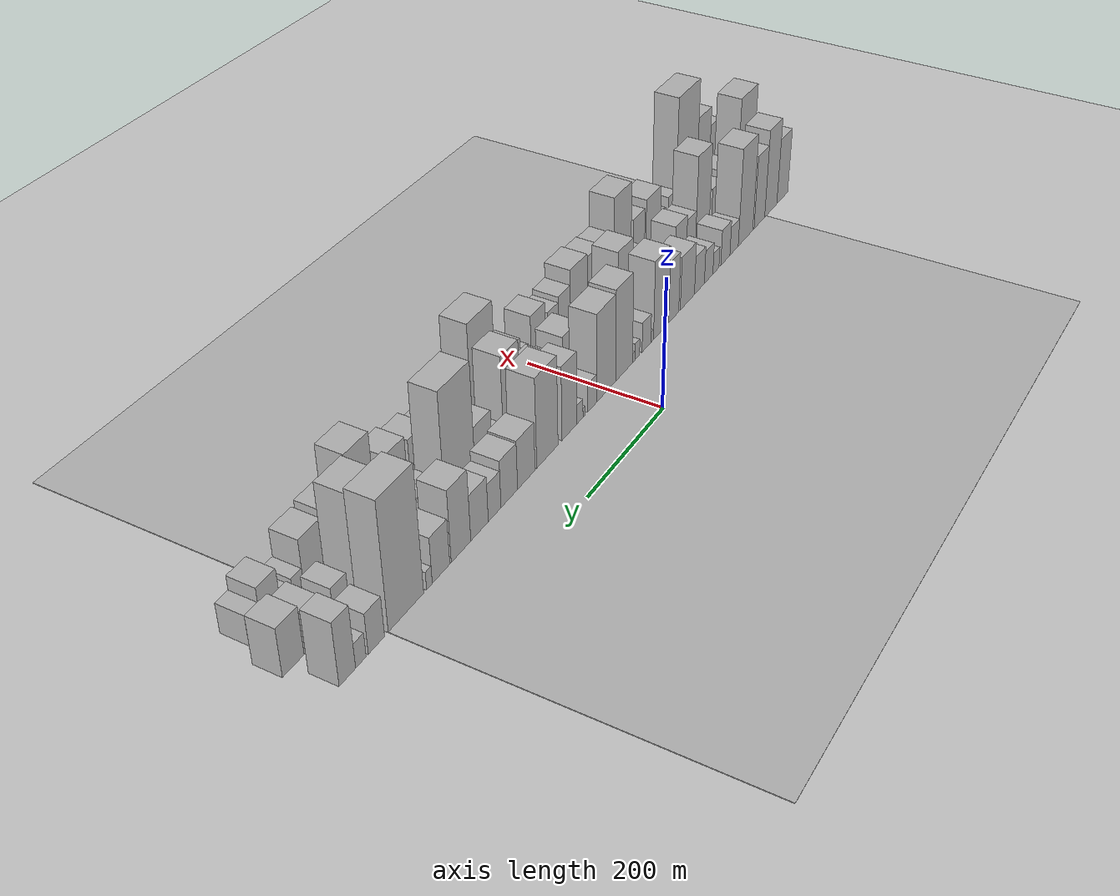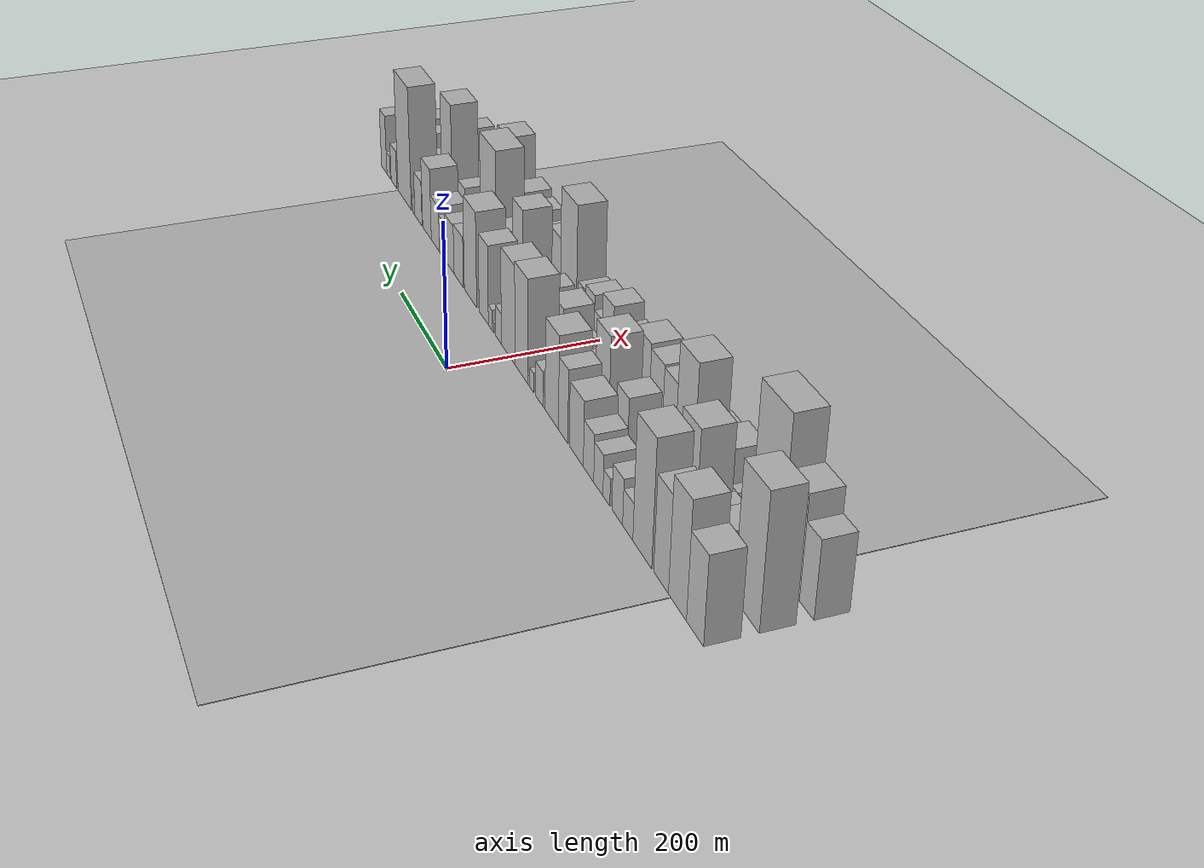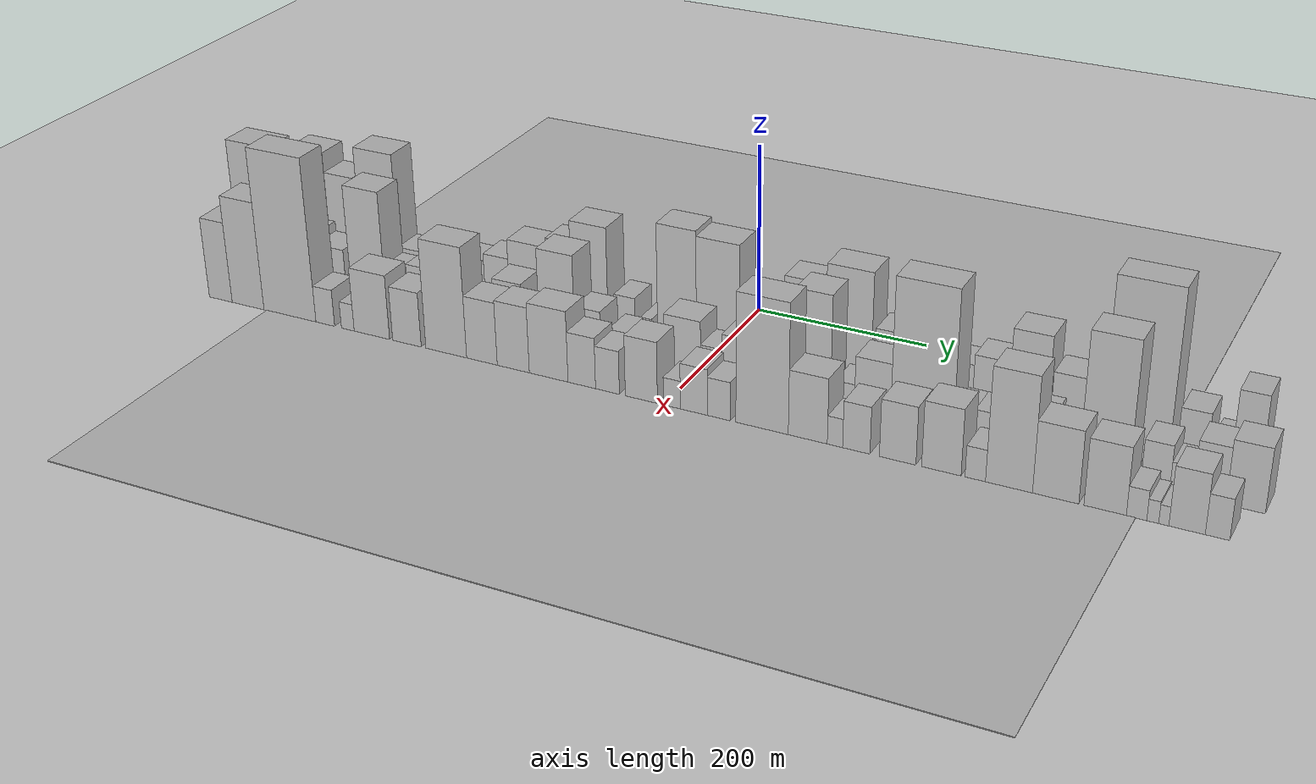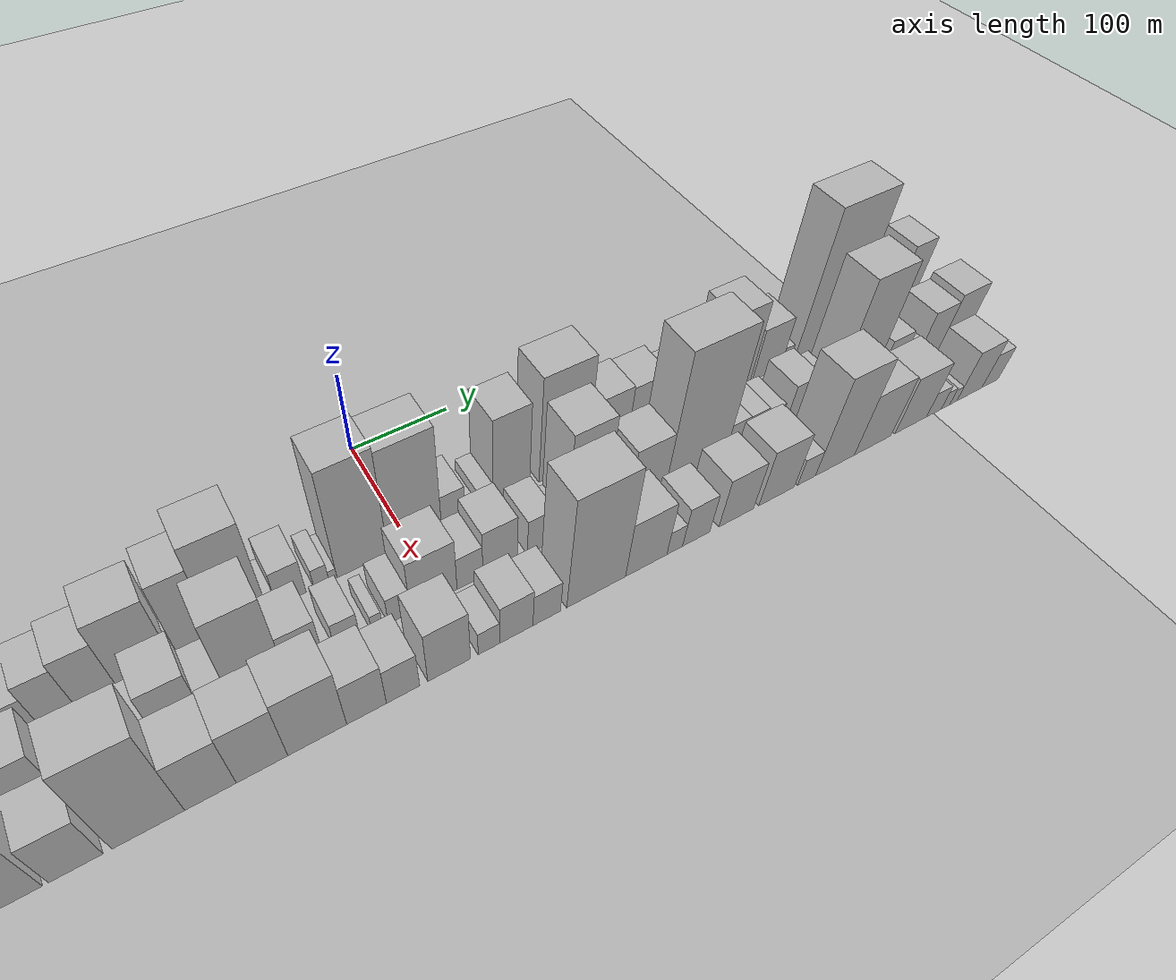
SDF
<?xml version="1.0" encoding="utf-8"?>

<sdf version="1.6">

   <world name="default">

      <gui fullscreen="0">

         <camera name="user_camera">

            <pose>-15 0 4.57585 0 0 0</pose>

            <view_controller>orbit</view_controller>

         </camera>

      </gui>

      <scene>

         <sky>

           <clouds>

             <speed>12</speed>

           </clouds>

         </sky>

         <ambient>0.4 0.4 0.4 1</ambient>

         <background>0.7 0.7 0.7 1</background>

         <shadows>1</shadows>

      </scene>

      <gravity>0 0 -9.8066</gravity>

      <magnetic_field>6e-06 2.3e-05 -4.2e-05</magnetic_field>

      <physics default="0" name="default_physics" type="ode">

         <ode>

            <solver>

               <type>quick</type>

               <iters>10</iters>

               <sor>1.0</sor>

               <use_dynamic_moi_rescaling>0</use_dynamic_moi_rescaling>

            </solver>

            <constraints>

               <cfm>0</cfm>

               <erp>0.2</erp>

               <contact_max_correcting_vel>100</contact_max_correcting_vel>

               <contact_surface_layer>0.001</contact_surface_layer>

            </constraints>

         </ode>

         <max_step_size>0.004</max_step_size>

         <real_time_factor>1</real_time_factor>

         <real_time_update_rate>250</real_time_update_rate>

      </physics>

      <light name="sun" type="directional">

         <cast_shadows>1</cast_shadows>

         <pose>0 0 10 0 0 0</pose>

         <diffuse>0.8 0.8 0.8 1</diffuse>

         <specular>0.2 0.2 0.2 1</specular>

         <attenuation>

            <range>1000</range>

            <constant>0.9</constant>

            <linear>0.01</linear>

            <quadratic>0.001</quadratic>

         </attenuation>

         <direction>-0.5 0.1 -0.9</direction>

      </light>

      <include>

         <name>ground_plane_1</name>

         <uri>model://HANNAS_ground_plane</uri>

         <pose>0 0 0  0 0 0</pose>

      </include>

      <include>

         <name>ground_plane_2</name>

         <uri>model://HANNAS_ground_plane</uri>

         <pose>100 0 0  0 0 0</pose>

      </include>

      <model name="building_1">

         <static>1</static>

         <pose frame="">100.0000 -559.4491 0 0.000000 0.000000 0.000000</pose>

         <link name="link">

            <pose frame="">0 0 55.50 0 0 0</pose>

            <collision name="collision">

               <geometry>

                  <box>

                     <size>40.0000 41.1019 111.0000</size>

                  </box>

               </geometry>

               <max_contacts>10</max_contacts>

               <surface>

                  <contact>

                     <ode/>

                  </contact>

                  <bounce/>

                  <friction>

                     <torsional>

                        <ode/>

                     </torsional>

                     <ode/>

                  </friction>

               </surface>

            </collision>

            <visual name="visual">

               <cast_shadows>0</cast_shadows>

               <geometry>

                  <box>

                     <size>40.0000 41.1019 111.0000</size>

                  </box>

               </geometry>

               <material>

                  <script>

                     <uri>model://HANNAS_wall/materials/scripts</uri>

                     <uri>model://HANNAS_wall/materials/textures</uri>

                     <name>vrc/HANNAS_wall</name>

                  </script>

               </material>

            </visual>

            <self_collide>0</self_collide>

            <enable_wind>0</enable_wind>

            <kinematic>0</kinematic>

         </link>

      </model>

      <model name="building_2">

         <static>1</static>

         <pose frame="">100.0000 -516.3879 0 0.000000 0.000000 0.000000</pose>

         <link name="link">

            <pose frame="">0 0 73.50 0 0 0</pose>

            <collision name="collision">

               <geometry>

                  <box>

                     <size>40.0000 45.0204 147.0000</size>

                  </box>

               </geometry>

               <max_contacts>10</max_contacts>

               <surface>

                  <contact>

                     <ode/>

                  </contact>

                  <bounce/>

                  <friction>

                     <torsional>

                        <ode/>

                     </torsional>

                     <ode/>

                  </friction>

               </surface>

            </collision>

            <visual name="visual">

               <cast_shadows>0</cast_shadows>

               <geometry>

                  <box>

                     <size>40.0000 45.0204 147.0000</size>

                  </box>

               </geometry>

               <material>

                  <script>

                     <uri>model://HANNAS_wall/materials/scripts</uri>

                     <uri>model://HANNAS_wall/materials/textures</uri>

                     <name>vrc/HANNAS_wall</name>

                  </script>

               </material>

            </visual>

            <self_collide>0</self_collide>

            <enable_wind>0</enable_wind>

            <kinematic>0</kinematic>

         </link>

      </model>

      <model name="building_3">

         <static>1</static>

         <pose frame="">100.0000 -474.6884 0 0.000000 0.000000 0.000000</pose>

         <link name="link">

            <pose frame="">0 0 61.50 0 0 0</pose>

            <collision name="collision">

               <geometry>

                  <box>

                     <size>40.0000 38.3787 123.0000</size>

                  </box>

               </geometry>

               <max_contacts>10</max_contacts>

               <surface>

                  <contact>

                     <ode/>

                  </contact>

                  <bounce/>

                  <friction>

                     <torsional>

                        <ode/>

                     </torsional>

                     <ode/>

                  </friction>

               </surface>

            </collision>

            <visual name="visual">

               <cast_shadows>0</cast_shadows>

               <geometry>

                  <box>

                     <size>40.0000 38.3787 123.0000</size>

                  </box>

               </geometry>

               <material>

                  <script>

                     <uri>model://HANNAS_wall/materials/scripts</uri>

                     <uri>model://HANNAS_wall/materials/textures</uri>

                     <name>vrc/HANNAS_wall</name>

                  </script>

               </material>

            </visual>

            <self_collide>0</self_collide>

            <enable_wind>0</enable_wind>

            <kinematic>0</kinematic>

         </link>

      </model>

      <model name="building_4">

         <static>1</static>

         <pose frame="">100.0000 -424.9814 0 0.000000 0.000000 0.000000</pose>

         <link name="link">

            <pose frame="">0 0 81.00 0 0 0</pose>

            <collision name="collision">

               <geometry>

                  <box>

                     <size>40.0000 51.0353 162.0000</size>

                  </box>

               </geometry>

               <max_contacts>10</max_contacts>

               <surface>

                  <contact>

                     <ode/>

                  </contact>

                  <bounce/>

                  <friction>

                     <torsional>

                        <ode/>

                     </torsional>

                     <ode/>

                  </friction>

               </surface>

            </collision>

            <visual name="visual">

               <cast_shadows>0</cast_shadows>

               <geometry>

                  <box>

                     <size>40.0000 51.0353 162.0000</size>

                  </box>

               </geometry>

               <material>

                  <script>

                     <uri>model://HANNAS_wall/materials/scripts</uri>

                     <uri>model://HANNAS_wall/materials/textures</uri>

                     <name>vrc/HANNAS_wall</name>

                  </script>

               </material>

            </visual>

            <self_collide>0</self_collide>

            <enable_wind>0</enable_wind>

            <kinematic>0</kinematic>

         </link>

      </model>

      <model name="building_5">

         <static>1</static>

         <pose frame="">100.0000 -385.1434 0 0.000000 0.000000 0.000000</pose>

         <link name="link">

            <pose frame="">0 0 24.00 0 0 0</pose>

            <collision name="collision">

               <geometry>

                  <box>

                     <size>40.0000 28.6407 48.0000</size>

                  </box>

               </geometry>

               <max_contacts>10</max_contacts>

               <surface>

                  <contact>

                     <ode/>

                  </contact>

                  <bounce/>

                  <friction>

                     <torsional>

                        <ode/>

                     </torsional>

                     <ode/>

                  </friction>

               </surface>

            </collision>

            <visual name="visual">

               <cast_shadows>0</cast_shadows>

               <geometry>

                  <box>

                     <size>40.0000 28.6407 48.0000</size>

                  </box>

               </geometry>

               <material>

                  <script>

                     <uri>model://HANNAS_wall/materials/scripts</uri>

                     <uri>model://HANNAS_wall/materials/textures</uri>

                     <name>vrc/HANNAS_wall</name>

                  </script>

               </material>

            </visual>

            <self_collide>0</self_collide>

            <enable_wind>0</enable_wind>

            <kinematic>0</kinematic>

         </link>

      </model>

      <model name="building_6">

         <static>1</static>

         <pose frame="">100.0000 -355.3499 0 0.000000 0.000000 0.000000</pose>

         <link name="link">

            <pose frame="">0 0 30.00 0 0 0</pose>

            <collision name="collision">

               <geometry>

                  <box>

                     <size>40.0000 30.9463 60.0000</size>

                  </box>

               </geometry>

               <max_contacts>10</max_contacts>

               <surface>

                  <contact>

                     <ode/>

                  </contact>

                  <bounce/>

                  <friction>

                     <torsional>

                        <ode/>

                     </torsional>

                     <ode/>

                  </friction>

               </surface>

            </collision>

            <visual name="visual">

               <cast_shadows>0</cast_shadows>

               <geometry>

                  <box>

                     <size>40.0000 30.9463 60.0000</size>

                  </box>

               </geometry>

               <material>

                  <script>

                     <uri>model://HANNAS_wall/materials/scripts</uri>

                     <uri>model://HANNAS_wall/materials/textures</uri>

                     <name>vrc/HANNAS_wall</name>

                  </script>

               </material>

            </visual>

            <self_collide>0</self_collide>

            <enable_wind>0</enable_wind>

            <kinematic>0</kinematic>

         </link>

      </model>

      <model name="building_7">

         <static>1</static>

         <pose frame="">100.0000 -323.7551 0 0.000000 0.000000 0.000000</pose>

         <link name="link">

            <pose frame="">0 0 18.00 0 0 0</pose>

            <collision name="collision">

               <geometry>

                  <box>

                     <size>40.0000 20.2433 36.0000</size>

                  </box>

               </geometry>

               <max_contacts>10</max_contacts>

               <surface>

                  <contact>

                     <ode/>

                  </contact>

                  <bounce/>

                  <friction>

                     <torsional>

                        <ode/>

                     </torsional>

                     <ode/>

                  </friction>

               </surface>

            </collision>

            <visual name="visual">

               <cast_shadows>0</cast_shadows>

               <geometry>

                  <box>

                     <size>40.0000 20.2433 36.0000</size>

                  </box>

               </geometry>

               <material>

                  <script>

                     <uri>model://HANNAS_wall/materials/scripts</uri>

                     <uri>model://HANNAS_wall/materials/textures</uri>

                     <name>vrc/HANNAS_wall</name>

                  </script>

               </material>

            </visual>

            <self_collide>0</self_collide>

            <enable_wind>0</enable_wind>

            <kinematic>0</kinematic>

         </link>

      </model>

      <model name="building_8">

         <static>1</static>

         <pose frame="">100.0000 -299.7620 0 0.000000 0.000000 0.000000</pose>

         <link name="link">

            <pose frame="">0 0 27.00 0 0 0</pose>

            <collision name="collision">

               <geometry>

                  <box>

                     <size>40.0000 27.7428 54.0000</size>

                  </box>

               </geometry>

               <max_contacts>10</max_contacts>

               <surface>

                  <contact>

                     <ode/>

                  </contact>

                  <bounce/>

                  <friction>

                     <torsional>

                        <ode/>

                     </torsional>

                     <ode/>

                  </friction>

               </surface>

            </collision>

            <visual name="visual">

               <cast_shadows>0</cast_shadows>

               <geometry>

                  <box>

                     <size>40.0000 27.7428 54.0000</size>

                  </box>

               </geometry>

               <material>

                  <script>

                     <uri>model://HANNAS_wall/materials/scripts</uri>

                     <uri>model://HANNAS_wall/materials/textures</uri>

                     <name>vrc/HANNAS_wall</name>

                  </script>

               </material>

            </visual>

            <self_collide>0</self_collide>

            <enable_wind>0</enable_wind>

            <kinematic>0</kinematic>

         </link>

      </model>

      <model name="building_9">

         <static>1</static>

         <pose frame="">100.0000 -269.9107 0 0.000000 0.000000 0.000000</pose>

         <link name="link">

            <pose frame="">0 0 31.50 0 0 0</pose>

            <collision name="collision">

               <geometry>

                  <box>

                     <size>40.0000 31.9600 63.0000</size>

                  </box>

               </geometry>

               <max_contacts>10</max_contacts>

               <surface>

                  <contact>

                     <ode/>

                  </contact>

                  <bounce/>

                  <friction>

                     <torsional>

                        <ode/>

                     </torsional>

                     <ode/>

                  </friction>

               </surface>

            </collision>

            <visual name="visual">

               <cast_shadows>0</cast_shadows>

               <geometry>

                  <box>

                     <size>40.0000 31.9600 63.0000</size>

                  </box>

               </geometry>

               <material>

                  <script>

                     <uri>model://HANNAS_wall/materials/scripts</uri>

                     <uri>model://HANNAS_wall/materials/textures</uri>

                     <name>vrc/HANNAS_wall</name>

                  </script>

               </material>

            </visual>

            <self_collide>0</self_collide>

            <enable_wind>0</enable_wind>

            <kinematic>0</kinematic>

         </link>

      </model>

      <model name="building_10">

         <static>1</static>

         <pose frame="">100.0000 -231.6543 0 0.000000 0.000000 0.000000</pose>

         <link name="link">

            <pose frame="">0 0 43.50 0 0 0</pose>

            <collision name="collision">

               <geometry>

                  <box>

                     <size>40.0000 44.5528 87.0000</size>

                  </box>

               </geometry>

               <max_contacts>10</max_contacts>

               <surface>

                  <contact>

                     <ode/>

                  </contact>

                  <bounce/>

                  <friction>

                     <torsional>

                        <ode/>

                     </torsional>

                     <ode/>

                  </friction>

               </surface>

            </collision>

            <visual name="visual">

               <cast_shadows>0</cast_shadows>

               <geometry>

                  <box>

                     <size>40.0000 44.5528 87.0000</size>

                  </box>

               </geometry>

               <material>

                  <script>

                     <uri>model://HANNAS_wall/materials/scripts</uri>

                     <uri>model://HANNAS_wall/materials/textures</uri>

                     <name>vrc/HANNAS_wall</name>

                  </script>

               </material>

            </visual>

            <self_collide>0</self_collide>

            <enable_wind>0</enable_wind>

            <kinematic>0</kinematic>

         </link>

      </model>

      <model name="building_11">

         <static>1</static>

         <pose frame="">100.0000 -189.0056 0 0.000000 0.000000 0.000000</pose>

         <link name="link">

            <pose frame="">0 0 49.50 0 0 0</pose>

            <collision name="collision">

               <geometry>

                  <box>

                     <size>40.0000 30.7445 99.0000</size>

                  </box>

               </geometry>

               <max_contacts>10</max_contacts>

               <surface>

                  <contact>

                     <ode/>

                  </contact>

                  <bounce/>

                  <friction>

                     <torsional>

                        <ode/>

                     </torsional>

                     <ode/>

                  </friction>

               </surface>

            </collision>

            <visual name="visual">

               <cast_shadows>0</cast_shadows>

               <geometry>

                  <box>

                     <size>40.0000 30.7445 99.0000</size>

                  </box>

               </geometry>

               <material>

                  <script>

                     <uri>model://HANNAS_wall/materials/scripts</uri>

                     <uri>model://HANNAS_wall/materials/textures</uri>

                     <name>vrc/HANNAS_wall</name>

                  </script>

               </material>

            </visual>

            <self_collide>0</self_collide>

            <enable_wind>0</enable_wind>

            <kinematic>0</kinematic>

         </link>

      </model>

      <model name="building_12">

         <static>1</static>

         <pose frame="">100.0000 -151.0599 0 0.000000 0.000000 0.000000</pose>

         <link name="link">

            <pose frame="">0 0 63.00 0 0 0</pose>

            <collision name="collision">

               <geometry>

                  <box>

                     <size>40.0000 45.1471 126.0000</size>

                  </box>

               </geometry>

               <max_contacts>10</max_contacts>

               <surface>

                  <contact>

                     <ode/>

                  </contact>

                  <bounce/>

                  <friction>

                     <torsional>

                        <ode/>

                     </torsional>

                     <ode/>

                  </friction>

               </surface>

            </collision>

            <visual name="visual">

               <cast_shadows>0</cast_shadows>

               <geometry>

                  <box>

                     <size>40.0000 45.1471 126.0000</size>

                  </box>

               </geometry>

               <material>

                  <script>

                     <uri>model://HANNAS_wall/materials/scripts</uri>

                     <uri>model://HANNAS_wall/materials/textures</uri>

                     <name>vrc/HANNAS_wall</name>

                  </script>

               </material>

            </visual>

            <self_collide>0</self_collide>

            <enable_wind>0</enable_wind>

            <kinematic>0</kinematic>

         </link>

      </model>

      <model name="building_13">

         <static>1</static>

         <pose frame="">100.0000 -124.5422 0 0.000000 0.000000 0.000000</pose>

         <link name="link">

            <pose frame="">0 0 9.00 0 0 0</pose>

            <collision name="collision">

               <geometry>

                  <box>

                     <size>40.0000 7.8883 18.0000</size>

                  </box>

               </geometry>

               <max_contacts>10</max_contacts>

               <surface>

                  <contact>

                     <ode/>

                  </contact>

                  <bounce/>

                  <friction>

                     <torsional>

                        <ode/>

                     </torsional>

                     <ode/>

                  </friction>

               </surface>

            </collision>

            <visual name="visual">

               <cast_shadows>0</cast_shadows>

               <geometry>

                  <box>

                     <size>40.0000 7.8883 18.0000</size>

                  </box>

               </geometry>

               <material>

                  <script>

                     <uri>model://HANNAS_wall/materials/scripts</uri>

                     <uri>model://HANNAS_wall/materials/textures</uri>

                     <name>vrc/HANNAS_wall</name>

                  </script>

               </material>

            </visual>

            <self_collide>0</self_collide>

            <enable_wind>0</enable_wind>

            <kinematic>0</kinematic>

         </link>

      </model>

      <model name="building_14">

         <static>1</static>

         <pose frame="">100.0000 -107.7938 0 0.000000 0.000000 0.000000</pose>

         <link name="link">

            <pose frame="">0 0 24.00 0 0 0</pose>

            <collision name="collision">

               <geometry>

                  <box>

                     <size>40.0000 25.6084 48.0000</size>

                  </box>

               </geometry>

               <max_contacts>10</max_contacts>

               <surface>

                  <contact>

                     <ode/>

                  </contact>

                  <bounce/>

                  <friction>

                     <torsional>

                        <ode/>

                     </torsional>

                     <ode/>

                  </friction>

               </surface>

            </collision>

            <visual name="visual">

               <cast_shadows>0</cast_shadows>

               <geometry>

                  <box>

                     <size>40.0000 25.6084 48.0000</size>

                  </box>

               </geometry>

               <material>

                  <script>

                     <uri>model://HANNAS_wall/materials/scripts</uri>

                     <uri>model://HANNAS_wall/materials/textures</uri>

                     <name>vrc/HANNAS_wall</name>

                  </script>

               </material>

            </visual>

            <self_collide>0</self_collide>

            <enable_wind>0</enable_wind>

            <kinematic>0</kinematic>

         </link>

      </model>

      <model name="building_15">

         <static>1</static>

         <pose frame="">100.0000 -81.2954 0 0.000000 0.000000 0.000000</pose>

         <link name="link">

            <pose frame="">0 0 13.50 0 0 0</pose>

            <collision name="collision">

               <geometry>

                  <box>

                     <size>40.0000 13.3885 27.0000</size>

                  </box>

               </geometry>

               <max_contacts>10</max_contacts>

               <surface>

                  <contact>

                     <ode/>

                  </contact>

                  <bounce/>

                  <friction>

                     <torsional>

                        <ode/>

                     </torsional>

                     <ode/>

                  </friction>

               </surface>

            </collision>

            <visual name="visual">

               <cast_shadows>0</cast_shadows>

               <geometry>

                  <box>

                     <size>40.0000 13.3885 27.0000</size>

                  </box>

               </geometry>

               <material>

                  <script>

                     <uri>model://HANNAS_wall/materials/scripts</uri>

                     <uri>model://HANNAS_wall/materials/textures</uri>

                     <name>vrc/HANNAS_wall</name>

                  </script>

               </material>

            </visual>

            <self_collide>0</self_collide>

            <enable_wind>0</enable_wind>

            <kinematic>0</kinematic>

         </link>

      </model>

      <model name="building_16">

         <static>1</static>

         <pose frame="">100.0000 -70.9838 0 0.000000 0.000000 0.000000</pose>

         <link name="link">

            <pose frame="">0 0 7.50 0 0 0</pose>

            <collision name="collision">

               <geometry>

                  <box>

                     <size>40.0000 7.2346 15.0000</size>

                  </box>

               </geometry>

               <max_contacts>10</max_contacts>

               <surface>

                  <contact>

                     <ode/>

                  </contact>

                  <bounce/>

                  <friction>

                     <torsional>

                        <ode/>

                     </torsional>

                     <ode/>

                  </friction>

               </surface>

            </collision>

            <visual name="visual">

               <cast_shadows>0</cast_shadows>

               <geometry>

                  <box>

                     <size>40.0000 7.2346 15.0000</size>

                  </box>

               </geometry>

               <material>

                  <script>

                     <uri>model://HANNAS_wall/materials/scripts</uri>

                     <uri>model://HANNAS_wall/materials/textures</uri>

                     <name>vrc/HANNAS_wall</name>

                  </script>

               </material>

            </visual>

            <self_collide>0</self_collide>

            <enable_wind>0</enable_wind>

            <kinematic>0</kinematic>

         </link>

      </model>

      <model name="building_17">

         <static>1</static>

         <pose frame="">100.0000 -43.8087 0 0.000000 0.000000 0.000000</pose>

         <link name="link">

            <pose frame="">0 0 72.00 0 0 0</pose>

            <collision name="collision">

               <geometry>

                  <box>

                     <size>40.0000 47.1157 144.0000</size>

                  </box>

               </geometry>

               <max_contacts>10</max_contacts>

               <surface>

                  <contact>

                     <ode/>

                  </contact>

                  <bounce/>

                  <friction>

                     <torsional>

                        <ode/>

                     </torsional>

                     <ode/>

                  </friction>

               </surface>

            </collision>

            <visual name="visual">

               <cast_shadows>0</cast_shadows>

               <geometry>

                  <box>

                     <size>40.0000 47.1157 144.0000</size>

                  </box>

               </geometry>

               <material>

                  <script>

                     <uri>model://HANNAS_wall/materials/scripts</uri>

                     <uri>model://HANNAS_wall/materials/textures</uri>

                     <name>vrc/HANNAS_wall</name>

                  </script>

               </material>

            </visual>

            <self_collide>0</self_collide>

            <enable_wind>0</enable_wind>

            <kinematic>0</kinematic>

         </link>

      </model>

      <model name="building_18">

         <static>1</static>

         <pose frame="">100.0000 5.4919 0 0.000000 0.000000 0.000000</pose>

         <link name="link">

            <pose frame="">0 0 69.00 0 0 0</pose>

            <collision name="collision">

               <geometry>

                  <box>

                     <size>40.0000 51.4854 138.0000</size>

                  </box>

               </geometry>

               <max_contacts>10</max_contacts>

               <surface>

                  <contact>

                     <ode/>

                  </contact>

                  <bounce/>

                  <friction>

                     <torsional>

                        <ode/>

                     </torsional>

                     <ode/>

                  </friction>

               </surface>

            </collision>

            <visual name="visual">

               <cast_shadows>0</cast_shadows>

               <geometry>

                  <box>

                     <size>40.0000 51.4854 138.0000</size>

                  </box>

               </geometry>

               <material>

                  <script>

                     <uri>model://HANNAS_wall/materials/scripts</uri>

                     <uri>model://HANNAS_wall/materials/textures</uri>

                     <name>vrc/HANNAS_wall</name>

                  </script>

               </material>

            </visual>

            <self_collide>0</self_collide>

            <enable_wind>0</enable_wind>

            <kinematic>0</kinematic>

         </link>

      </model>

      <model name="building_19">

         <static>1</static>

         <pose frame="">100.0000 42.9198 0 0.000000 0.000000 0.000000</pose>

         <link name="link">

            <pose frame="">0 0 22.50 0 0 0</pose>

            <collision name="collision">

               <geometry>

                  <box>

                     <size>40.0000 23.3706 45.0000</size>

                  </box>

               </geometry>

               <max_contacts>10</max_contacts>

               <surface>

                  <contact>

                     <ode/>

                  </contact>

                  <bounce/>

                  <friction>

                     <torsional>

                        <ode/>

                     </torsional>

                     <ode/>

                  </friction>

               </surface>

            </collision>

            <visual name="visual">

               <cast_shadows>0</cast_shadows>

               <geometry>

                  <box>

                     <size>40.0000 23.3706 45.0000</size>

                  </box>

               </geometry>

               <material>

                  <script>

                     <uri>model://HANNAS_wall/materials/scripts</uri>

                     <uri>model://HANNAS_wall/materials/textures</uri>

                     <name>vrc/HANNAS_wall</name>

                  </script>

               </material>

            </visual>

            <self_collide>0</self_collide>

            <enable_wind>0</enable_wind>

            <kinematic>0</kinematic>

         </link>

      </model>

      <model name="building_20">

         <static>1</static>

         <pose frame="">100.0000 63.7424 0 0.000000 0.000000 0.000000</pose>

         <link name="link">

            <pose frame="">0 0 7.50 0 0 0</pose>

            <collision name="collision">

               <geometry>

                  <box>

                     <size>40.0000 6.2745 15.0000</size>

                  </box>

               </geometry>

               <max_contacts>10</max_contacts>

               <surface>

                  <contact>

                     <ode/>

                  </contact>

                  <bounce/>

                  <friction>

                     <torsional>

                        <ode/>

                     </torsional>

                     <ode/>

                  </friction>

               </surface>

            </collision>

            <visual name="visual">

               <cast_shadows>0</cast_shadows>

               <geometry>

                  <box>

                     <size>40.0000 6.2745 15.0000</size>

                  </box>

               </geometry>

               <material>

                  <script>

                     <uri>model://HANNAS_wall/materials/scripts</uri>

                     <uri>model://HANNAS_wall/materials/textures</uri>

                     <name>vrc/HANNAS_wall</name>

                  </script>

               </material>

            </visual>

            <self_collide>0</self_collide>

            <enable_wind>0</enable_wind>

            <kinematic>0</kinematic>

         </link>

      </model>

      <model name="building_21">

         <static>1</static>

         <pose frame="">100.0000 74.7954 0 0.000000 0.000000 0.000000</pose>

         <link name="link">

            <pose frame="">0 0 15.00 0 0 0</pose>

            <collision name="collision">

               <geometry>

                  <box>

                     <size>40.0000 15.8314 30.0000</size>

                  </box>

               </geometry>

               <max_contacts>10</max_contacts>

               <surface>

                  <contact>

                     <ode/>

                  </contact>

                  <bounce/>

                  <friction>

                     <torsional>

                        <ode/>

                     </torsional>

                     <ode/>

                  </friction>

               </surface>

            </collision>

            <visual name="visual">

               <cast_shadows>0</cast_shadows>

               <geometry>

                  <box>

                     <size>40.0000 15.8314 30.0000</size>

                  </box>

               </geometry>

               <material>

                  <script>

                     <uri>model://HANNAS_wall/materials/scripts</uri>

                     <uri>model://HANNAS_wall/materials/textures</uri>

                     <name>vrc/HANNAS_wall</name>

                  </script>

               </material>

            </visual>

            <self_collide>0</self_collide>

            <enable_wind>0</enable_wind>

            <kinematic>0</kinematic>

         </link>

      </model>

      <model name="building_22">

         <static>1</static>

         <pose frame="">100.0000 101.5277 0 0.000000 0.000000 0.000000</pose>

         <link name="link">

            <pose frame="">0 0 57.00 0 0 0</pose>

            <collision name="collision">

               <geometry>

                  <box>

                     <size>40.0000 37.6332 114.0000</size>

                  </box>

               </geometry>

               <max_contacts>10</max_contacts>

               <surface>

                  <contact>

                     <ode/>

                  </contact>

                  <bounce/>

                  <friction>

                     <torsional>

                        <ode/>

                     </torsional>

                     <ode/>

                  </friction>

               </surface>

            </collision>

            <visual name="visual">

               <cast_shadows>0</cast_shadows>

               <geometry>

                  <box>

                     <size>40.0000 37.6332 114.0000</size>

                  </box>

               </geometry>

               <material>

                  <script>

                     <uri>model://HANNAS_wall/materials/scripts</uri>

                     <uri>model://HANNAS_wall/materials/textures</uri>

                     <name>vrc/HANNAS_wall</name>

                  </script>

               </material>

            </visual>

            <self_collide>0</self_collide>

            <enable_wind>0</enable_wind>

            <kinematic>0</kinematic>

         </link>

      </model>

      <model name="building_23">

         <static>1</static>

         <pose frame="">100.0000 156.4455 0 0.000000 0.000000 0.000000</pose>

         <link name="link">

            <pose frame="">0 0 69.00 0 0 0</pose>

            <collision name="collision">

               <geometry>

                  <box>

                     <size>40.0000 52.2026 138.0000</size>

                  </box>

               </geometry>

               <max_contacts>10</max_contacts>

               <surface>

                  <contact>

                     <ode/>

                  </contact>

                  <bounce/>

                  <friction>

                     <torsional>

                        <ode/>

                     </torsional>

                     <ode/>

                  </friction>

               </surface>

            </collision>

            <visual name="visual">

               <cast_shadows>0</cast_shadows>

               <geometry>

                  <box>

                     <size>40.0000 52.2026 138.0000</size>

                  </box>

               </geometry>

               <material>

                  <script>

                     <uri>model://HANNAS_wall/materials/scripts</uri>

                     <uri>model://HANNAS_wall/materials/textures</uri>

                     <name>vrc/HANNAS_wall</name>

                  </script>

               </material>

            </visual>

            <self_collide>0</self_collide>

            <enable_wind>0</enable_wind>

            <kinematic>0</kinematic>

         </link>

      </model>

      <model name="building_24">

         <static>1</static>

         <pose frame="">100.0000 207.1209 0 0.000000 0.000000 0.000000</pose>

         <link name="link">

            <pose frame="">0 0 37.50 0 0 0</pose>

            <collision name="collision">

               <geometry>

                  <box>

                     <size>40.0000 41.1482 75.0000</size>

                  </box>

               </geometry>

               <max_contacts>10</max_contacts>

               <surface>

                  <contact>

                     <ode/>

                  </contact>

                  <bounce/>

                  <friction>

                     <torsional>

                        <ode/>

                     </torsional>

                     <ode/>

                  </friction>

               </surface>

            </collision>

            <visual name="visual">

               <cast_shadows>0</cast_shadows>

               <geometry>

                  <box>

                     <size>40.0000 41.1482 75.0000</size>

                  </box>

               </geometry>

               <material>

                  <script>

                     <uri>model://HANNAS_wall/materials/scripts</uri>

                     <uri>model://HANNAS_wall/materials/textures</uri>

                     <name>vrc/HANNAS_wall</name>

                  </script>

               </material>

            </visual>

            <self_collide>0</self_collide>

            <enable_wind>0</enable_wind>

            <kinematic>0</kinematic>

         </link>

      </model>

      <model name="building_25">

         <static>1</static>

         <pose frame="">100.0000 246.7359 0 0.000000 0.000000 0.000000</pose>

         <link name="link">

            <pose frame="">0 0 36.00 0 0 0</pose>

            <collision name="collision">

               <geometry>

                  <box>

                     <size>40.0000 38.0818 72.0000</size>

                  </box>

               </geometry>

               <max_contacts>10</max_contacts>

               <surface>

                  <contact>

                     <ode/>

                  </contact>

                  <bounce/>

                  <friction>

                     <torsional>

                        <ode/>

                     </torsional>

                     <ode/>

                  </friction>

               </surface>

            </collision>

            <visual name="visual">

               <cast_shadows>0</cast_shadows>

               <geometry>

                  <box>

                     <size>40.0000 38.0818 72.0000</size>

                  </box>

               </geometry>

               <material>

                  <script>

                     <uri>model://HANNAS_wall/materials/scripts</uri>

                     <uri>model://HANNAS_wall/materials/textures</uri>

                     <name>vrc/HANNAS_wall</name>

                  </script>

               </material>

            </visual>

            <self_collide>0</self_collide>

            <enable_wind>0</enable_wind>

            <kinematic>0</kinematic>

         </link>

      </model>

      <model name="building_26">

         <static>1</static>

         <pose frame="">100.0000 280.0626 0 0.000000 0.000000 0.000000</pose>

         <link name="link">

            <pose frame="">0 0 28.50 0 0 0</pose>

            <collision name="collision">

               <geometry>

                  <box>

                     <size>40.0000 28.5716 57.0000</size>

                  </box>

               </geometry>

               <max_contacts>10</max_contacts>

               <surface>

                  <contact>

                     <ode/>

                  </contact>

                  <bounce/>

                  <friction>

                     <torsional>

                        <ode/>

                     </torsional>

                     <ode/>

                  </friction>

               </surface>

            </collision>

            <visual name="visual">

               <cast_shadows>0</cast_shadows>

               <geometry>

                  <box>

                     <size>40.0000 28.5716 57.0000</size>

                  </box>

               </geometry>

               <material>

                  <script>

                     <uri>model://HANNAS_wall/materials/scripts</uri>

                     <uri>model://HANNAS_wall/materials/textures</uri>

                     <name>vrc/HANNAS_wall</name>

                  </script>

               </material>

            </visual>

            <self_collide>0</self_collide>

            <enable_wind>0</enable_wind>

            <kinematic>0</kinematic>

         </link>

      </model>

      <model name="building_27">

         <static>1</static>

         <pose frame="">100.0000 313.5556 0 0.000000 0.000000 0.000000</pose>

         <link name="link">

            <pose frame="">0 0 34.50 0 0 0</pose>

            <collision name="collision">

               <geometry>

                  <box>

                     <size>40.0000 38.4144 69.0000</size>

                  </box>

               </geometry>

               <max_contacts>10</max_contacts>

               <surface>

                  <contact>

                     <ode/>

                  </contact>

                  <bounce/>

                  <friction>

                     <torsional>

                        <ode/>

                     </torsional>

                     <ode/>

                  </friction>

               </surface>

            </collision>

            <visual name="visual">

               <cast_shadows>0</cast_shadows>

               <geometry>

                  <box>

                     <size>40.0000 38.4144 69.0000</size>

                  </box>

               </geometry>

               <material>

                  <script>

                     <uri>model://HANNAS_wall/materials/scripts</uri>

                     <uri>model://HANNAS_wall/materials/textures</uri>

                     <name>vrc/HANNAS_wall</name>

                  </script>

               </material>

            </visual>

            <self_collide>0</self_collide>

            <enable_wind>0</enable_wind>

            <kinematic>0</kinematic>

         </link>

      </model>

      <model name="building_28">

         <static>1</static>

         <pose frame="">100.0000 353.5814 0 0.000000 0.000000 0.000000</pose>

         <link name="link">

            <pose frame="">0 0 54.00 0 0 0</pose>

            <collision name="collision">

               <geometry>

                  <box>

                     <size>40.0000 41.6372 108.0000</size>

                  </box>

               </geometry>

               <max_contacts>10</max_contacts>

               <surface>

                  <contact>

                     <ode/>

                  </contact>

                  <bounce/>

                  <friction>

                     <torsional>

                        <ode/>

                     </torsional>

                     <ode/>

                  </friction>

               </surface>

            </collision>

            <visual name="visual">

               <cast_shadows>0</cast_shadows>

               <geometry>

                  <box>

                     <size>40.0000 41.6372 108.0000</size>

                  </box>

               </geometry>

               <material>

                  <script>

                     <uri>model://HANNAS_wall/materials/scripts</uri>

                     <uri>model://HANNAS_wall/materials/textures</uri>

                     <name>vrc/HANNAS_wall</name>

                  </script>

               </material>

            </visual>

            <self_collide>0</self_collide>

            <enable_wind>0</enable_wind>

            <kinematic>0</kinematic>

         </link>

      </model>

      <model name="building_29">

         <static>1</static>

         <pose frame="">100.0000 395.4486 0 0.000000 0.000000 0.000000</pose>

         <link name="link">

            <pose frame="">0 0 34.50 0 0 0</pose>

            <collision name="collision">

               <geometry>

                  <box>

                     <size>40.0000 36.0972 69.0000</size>

                  </box>

               </geometry>

               <max_contacts>10</max_contacts>

               <surface>

                  <contact>

                     <ode/>

                  </contact>

                  <bounce/>

                  <friction>

                     <torsional>

                        <ode/>

                     </torsional>

                     <ode/>

                  </friction>

               </surface>

            </collision>

            <visual name="visual">

               <cast_shadows>0</cast_shadows>

               <geometry>

                  <box>

                     <size>40.0000 36.0972 69.0000</size>

                  </box>

               </geometry>

               <material>

                  <script>

                     <uri>model://HANNAS_wall/materials/scripts</uri>

                     <uri>model://HANNAS_wall/materials/textures</uri>

                     <name>vrc/HANNAS_wall</name>

                  </script>

               </material>

            </visual>

            <self_collide>0</self_collide>

            <enable_wind>0</enable_wind>

            <kinematic>0</kinematic>

         </link>

      </model>

      <model name="building_30">

         <static>1</static>

         <pose frame="">100.0000 419.2913 0 0.000000 0.000000 0.000000</pose>

         <link name="link">

            <pose frame="">0 0 13.50 0 0 0</pose>

            <collision name="collision">

               <geometry>

                  <box>

                     <size>40.0000 11.5883 27.0000</size>

                  </box>

               </geometry>

               <max_contacts>10</max_contacts>

               <surface>

                  <contact>

                     <ode/>

                  </contact>

                  <bounce/>

                  <friction>

                     <torsional>

                        <ode/>

                     </torsional>

                     <ode/>

                  </friction>

               </surface>

            </collision>

            <visual name="visual">

               <cast_shadows>0</cast_shadows>

               <geometry>

                  <box>

                     <size>40.0000 11.5883 27.0000</size>

                  </box>

               </geometry>

               <material>

                  <script>

                     <uri>model://HANNAS_wall/materials/scripts</uri>

                     <uri>model://HANNAS_wall/materials/textures</uri>

                     <name>vrc/HANNAS_wall</name>

                  </script>

               </material>

            </visual>

            <self_collide>0</self_collide>

            <enable_wind>0</enable_wind>

            <kinematic>0</kinematic>

         </link>

      </model>

      <model name="building_31">

         <static>1</static>

         <pose frame="">100.0000 465.6862 0 0.000000 0.000000 0.000000</pose>

         <link name="link">

            <pose frame="">0 0 94.50 0 0 0</pose>

            <collision name="collision">

               <geometry>

                  <box>

                     <size>40.0000 69.2014 189.0000</size>

                  </box>

               </geometry>

               <max_contacts>10</max_contacts>

               <surface>

                  <contact>

                     <ode/>

                  </contact>

                  <bounce/>

                  <friction>

                     <torsional>

                        <ode/>

                     </torsional>

                     <ode/>

                  </friction>

               </surface>

            </collision>

            <visual name="visual">

               <cast_shadows>0</cast_shadows>

               <geometry>

                  <box>

                     <size>40.0000 69.2014 189.0000</size>

                  </box>

               </geometry>

               <material>

                  <script>

                     <uri>model://HANNAS_wall/materials/scripts</uri>

                     <uri>model://HANNAS_wall/materials/textures</uri>

                     <name>vrc/HANNAS_wall</name>

                  </script>

               </material>

            </visual>

            <self_collide>0</self_collide>

            <enable_wind>0</enable_wind>

            <kinematic>0</kinematic>

         </link>

      </model>

      <model name="building_32">

         <static>1</static>

         <pose frame="">100.0000 522.4949 0 0.000000 0.000000 0.000000</pose>

         <link name="link">

            <pose frame="">0 0 30.00 0 0 0</pose>

            <collision name="collision">

               <geometry>

                  <box>

                     <size>40.0000 30.4160 60.0000</size>

                  </box>

               </geometry>

               <max_contacts>10</max_contacts>

               <surface>

                  <contact>

                     <ode/>

                  </contact>

                  <bounce/>

                  <friction>

                     <torsional>

                        <ode/>

                     </torsional>

                     <ode/>

                  </friction>

               </surface>

            </collision>

            <visual name="visual">

               <cast_shadows>0</cast_shadows>

               <geometry>

                  <box>

                     <size>40.0000 30.4160 60.0000</size>

                  </box>

               </geometry>

               <material>

                  <script>

                     <uri>model://HANNAS_wall/materials/scripts</uri>

                     <uri>model://HANNAS_wall/materials/textures</uri>

                     <name>vrc/HANNAS_wall</name>

                  </script>

               </material>

            </visual>

            <self_collide>0</self_collide>

            <enable_wind>0</enable_wind>

            <kinematic>0</kinematic>

         </link>

      </model>

      <model name="building_33">

         <static>1</static>

         <pose frame="">100.0000 551.3254 0 0.000000 0.000000 0.000000</pose>

         <link name="link">

            <pose frame="">0 0 18.00 0 0 0</pose>

            <collision name="collision">

               <geometry>

                  <box>

                     <size>40.0000 19.2451 36.0000</size>

                  </box>

               </geometry>

               <max_contacts>10</max_contacts>

               <surface>

                  <contact>

                     <ode/>

                  </contact>

                  <bounce/>

                  <friction>

                     <torsional>

                        <ode/>

                     </torsional>

                     <ode/>

                  </friction>

               </surface>

            </collision>

            <visual name="visual">

               <cast_shadows>0</cast_shadows>

               <geometry>

                  <box>

                     <size>40.0000 19.2451 36.0000</size>

                  </box>

               </geometry>

               <material>

                  <script>

                     <uri>model://HANNAS_wall/materials/scripts</uri>

                     <uri>model://HANNAS_wall/materials/textures</uri>

                     <name>vrc/HANNAS_wall</name>

                  </script>

               </material>

            </visual>

            <self_collide>0</self_collide>

            <enable_wind>0</enable_wind>

            <kinematic>0</kinematic>

         </link>

      </model>

      <model name="building_34">

         <static>1</static>

         <pose frame="">100.0000 575.7794 0 0.000000 0.000000 0.000000</pose>

         <link name="link">

            <pose frame="">0 0 46.50 0 0 0</pose>

            <collision name="collision">

               <geometry>

                  <box>

                     <size>40.0000 29.6628 93.0000</size>

                  </box>

               </geometry>

               <max_contacts>10</max_contacts>

               <surface>

                  <contact>

                     <ode/>

                  </contact>

                  <bounce/>

                  <friction>

                     <torsional>

                        <ode/>

                     </torsional>

                     <ode/>

                  </friction>

               </surface>

            </collision>

            <visual name="visual">

               <cast_shadows>0</cast_shadows>

               <geometry>

                  <box>

                     <size>40.0000 29.6628 93.0000</size>

                  </box>

               </geometry>

               <material>

                  <script>

                     <uri>model://HANNAS_wall/materials/scripts</uri>

                     <uri>model://HANNAS_wall/materials/textures</uri>

                     <name>vrc/HANNAS_wall</name>

                  </script>

               </material>

            </visual>

            <self_collide>0</self_collide>

            <enable_wind>0</enable_wind>

            <kinematic>0</kinematic>

         </link>

      </model>

      <model name="building_35">

         <static>1</static>

         <pose frame="">160.0000 -550.9667 0 0.000000 0.000000 0.000000</pose>

         <link name="link">

            <pose frame="">0 0 85.50 0 0 0</pose>

            <collision name="collision">

               <geometry>

                  <box>

                     <size>40.0000 58.0666 171.0000</size>

                  </box>

               </geometry>

               <max_contacts>10</max_contacts>

               <surface>

                  <contact>

                     <ode/>

                  </contact>

                  <bounce/>

                  <friction>

                     <torsional>

                        <ode/>

                     </torsional>

                     <ode/>

                  </friction>

               </surface>

            </collision>

            <visual name="visual">

               <cast_shadows>0</cast_shadows>

               <geometry>

                  <box>

                     <size>40.0000 58.0666 171.0000</size>

                  </box>

               </geometry>

               <material>

                  <script>

                     <uri>model://HANNAS_wall/materials/scripts</uri>

                     <uri>model://HANNAS_wall/materials/textures</uri>

                     <name>vrc/HANNAS_wall</name>

                  </script>

               </material>

            </visual>

            <self_collide>0</self_collide>

            <enable_wind>0</enable_wind>

            <kinematic>0</kinematic>

         </link>

      </model>

      <model name="building_36">

         <static>1</static>

         <pose frame="">160.0000 -516.1299 0 0.000000 0.000000 0.000000</pose>

         <link name="link">

            <pose frame="">0 0 13.50 0 0 0</pose>

            <collision name="collision">

               <geometry>

                  <box>

                     <size>40.0000 11.6070 27.0000</size>

                  </box>

               </geometry>

               <max_contacts>10</max_contacts>

               <surface>

                  <contact>

                     <ode/>

                  </contact>

                  <bounce/>

                  <friction>

                     <torsional>

                        <ode/>

                     </torsional>

                     <ode/>

                  </friction>

               </surface>

            </collision>

            <visual name="visual">

               <cast_shadows>0</cast_shadows>

               <geometry>

                  <box>

                     <size>40.0000 11.6070 27.0000</size>

                  </box>

               </geometry>

               <material>

                  <script>

                     <uri>model://HANNAS_wall/materials/scripts</uri>

                     <uri>model://HANNAS_wall/materials/textures</uri>

                     <name>vrc/HANNAS_wall</name>

                  </script>

               </material>

            </visual>

            <self_collide>0</self_collide>

            <enable_wind>0</enable_wind>

            <kinematic>0</kinematic>

         </link>

      </model>

      <model name="building_37">

         <static>1</static>

         <pose frame="">160.0000 -489.8425 0 0.000000 0.000000 0.000000</pose>

         <link name="link">

            <pose frame="">0 0 37.50 0 0 0</pose>

            <collision name="collision">

               <geometry>

                  <box>

                     <size>40.0000 40.9678 75.0000</size>

                  </box>

               </geometry>

               <max_contacts>10</max_contacts>

               <surface>

                  <contact>

                     <ode/>

                  </contact>

                  <bounce/>

                  <friction>

                     <torsional>

                        <ode/>

                     </torsional>

                     <ode/>

                  </friction>

               </surface>

            </collision>

            <visual name="visual">

               <cast_shadows>0</cast_shadows>

               <geometry>

                  <box>

                     <size>40.0000 40.9678 75.0000</size>

                  </box>

               </geometry>

               <material>

                  <script>

                     <uri>model://HANNAS_wall/materials/scripts</uri>

                     <uri>model://HANNAS_wall/materials/textures</uri>

                     <name>vrc/HANNAS_wall</name>

                  </script>

               </material>

            </visual>

            <self_collide>0</self_collide>

            <enable_wind>0</enable_wind>

            <kinematic>0</kinematic>

         </link>

      </model>

      <model name="building_38">

         <static>1</static>

         <pose frame="">160.0000 -450.9846 0 0.000000 0.000000 0.000000</pose>

         <link name="link">

            <pose frame="">0 0 31.50 0 0 0</pose>

            <collision name="collision">

               <geometry>

                  <box>

                     <size>40.0000 36.7479 63.0000</size>

                  </box>

               </geometry>

               <max_contacts>10</max_contacts>

               <surface>

                  <contact>

                     <ode/>

                  </contact>

                  <bounce/>

                  <friction>

                     <torsional>

                        <ode/>

                     </torsional>

                     <ode/>

                  </friction>

               </surface>

            </collision>

            <visual name="visual">

               <cast_shadows>0</cast_shadows>

               <geometry>

                  <box>

                     <size>40.0000 36.7479 63.0000</size>

                  </box>

               </geometry>

               <material>

                  <script>

                     <uri>model://HANNAS_wall/materials/scripts</uri>

                     <uri>model://HANNAS_wall/materials/textures</uri>

                     <name>vrc/HANNAS_wall</name>

                  </script>

               </material>

            </visual>

            <self_collide>0</self_collide>

            <enable_wind>0</enable_wind>

            <kinematic>0</kinematic>

         </link>

      </model>

      <model name="building_39">

         <static>1</static>

         <pose frame="">160.0000 -402.6543 0 0.000000 0.000000 0.000000</pose>

         <link name="link">

            <pose frame="">0 0 72.00 0 0 0</pose>

            <collision name="collision">

               <geometry>

                  <box>

                     <size>40.0000 45.9127 144.0000</size>

                  </box>

               </geometry>

               <max_contacts>10</max_contacts>

               <surface>

                  <contact>

                     <ode/>

                  </contact>

                  <bounce/>

                  <friction>

                     <torsional>

                        <ode/>

                     </torsional>

                     <ode/>

                  </friction>

               </surface>

            </collision>

            <visual name="visual">

               <cast_shadows>0</cast_shadows>

               <geometry>

                  <box>

                     <size>40.0000 45.9127 144.0000</size>

                  </box>

               </geometry>

               <material>

                  <script>

                     <uri>model://HANNAS_wall/materials/scripts</uri>

                     <uri>model://HANNAS_wall/materials/textures</uri>

                     <name>vrc/HANNAS_wall</name>

                  </script>

               </material>

            </visual>

            <self_collide>0</self_collide>

            <enable_wind>0</enable_wind>

            <kinematic>0</kinematic>

         </link>

      </model>

      <model name="building_40">

         <static>1</static>

         <pose frame="">160.0000 -364.5447 0 0.000000 0.000000 0.000000</pose>

         <link name="link">

            <pose frame="">0 0 27.00 0 0 0</pose>

            <collision name="collision">

               <geometry>

                  <box>

                     <size>40.0000 30.3064 54.0000</size>

                  </box>

               </geometry>

               <max_contacts>10</max_contacts>

               <surface>

                  <contact>

                     <ode/>

                  </contact>

                  <bounce/>

                  <friction>

                     <torsional>

                        <ode/>

                     </torsional>

                     <ode/>

                  </friction>

               </surface>

            </collision>

            <visual name="visual">

               <cast_shadows>0</cast_shadows>

               <geometry>

                  <box>

                     <size>40.0000 30.3064 54.0000</size>

                  </box>

               </geometry>

               <material>

                  <script>

                     <uri>model://HANNAS_wall/materials/scripts</uri>

                     <uri>model://HANNAS_wall/materials/textures</uri>

                     <name>vrc/HANNAS_wall</name>

                  </script>

               </material>

            </visual>

            <self_collide>0</self_collide>

            <enable_wind>0</enable_wind>

            <kinematic>0</kinematic>

         </link>

      </model>

      <model name="building_41">

         <static>1</static>

         <pose frame="">160.0000 -330.6106 0 0.000000 0.000000 0.000000</pose>

         <link name="link">

            <pose frame="">0 0 31.50 0 0 0</pose>

            <collision name="collision">

               <geometry>

                  <box>

                     <size>40.0000 37.5618 63.0000</size>

                  </box>

               </geometry>

               <max_contacts>10</max_contacts>

               <surface>

                  <contact>

                     <ode/>

                  </contact>

                  <bounce/>

                  <friction>

                     <torsional>

                        <ode/>

                     </torsional>

                     <ode/>

                  </friction>

               </surface>

            </collision>

            <visual name="visual">

               <cast_shadows>0</cast_shadows>

               <geometry>

                  <box>

                     <size>40.0000 37.5618 63.0000</size>

                  </box>

               </geometry>

               <material>

                  <script>

                     <uri>model://HANNAS_wall/materials/scripts</uri>

                     <uri>model://HANNAS_wall/materials/textures</uri>

                     <name>vrc/HANNAS_wall</name>

                  </script>

               </material>

            </visual>

            <self_collide>0</self_collide>

            <enable_wind>0</enable_wind>

            <kinematic>0</kinematic>

         </link>

      </model>

      <model name="building_42">

         <static>1</static>

         <pose frame="">160.0000 -220.6030 0 0.000000 0.000000 0.000000</pose>

         <link name="link">

            <pose frame="">0 0 34.50 0 0 0</pose>

            <collision name="collision">

               <geometry>

                  <box>

                     <size>40.0000 36.1512 69.0000</size>

                  </box>

               </geometry>

               <max_contacts>10</max_contacts>

               <surface>

                  <contact>

                     <ode/>

                  </contact>

                  <bounce/>

                  <friction>

                     <torsional>

                        <ode/>

                     </torsional>

                     <ode/>

                  </friction>

               </surface>

            </collision>

            <visual name="visual">

               <cast_shadows>0</cast_shadows>

               <geometry>

                  <box>

                     <size>40.0000 36.1512 69.0000</size>

                  </box>

               </geometry>

               <material>

                  <script>

                     <uri>model://HANNAS_wall/materials/scripts</uri>

                     <uri>model://HANNAS_wall/materials/textures</uri>

                     <name>vrc/HANNAS_wall</name>

                  </script>

               </material>

            </visual>

            <self_collide>0</self_collide>

            <enable_wind>0</enable_wind>

            <kinematic>0</kinematic>

         </link>

      </model>

      <model name="building_43">

         <static>1</static>

         <pose frame="">160.0000 -191.7162 0 0.000000 0.000000 0.000000</pose>

         <link name="link">

            <pose frame="">0 0 19.50 0 0 0</pose>

            <collision name="collision">

               <geometry>

                  <box>

                     <size>40.0000 21.6223 39.0000</size>

                  </box>

               </geometry>

               <max_contacts>10</max_contacts>

               <surface>

                  <contact>

                     <ode/>

                  </contact>

                  <bounce/>

                  <friction>

                     <torsional>

                        <ode/>

                     </torsional>

                     <ode/>

                  </friction>

               </surface>

            </collision>

            <visual name="visual">

               <cast_shadows>0</cast_shadows>

               <geometry>

                  <box>

                     <size>40.0000 21.6223 39.0000</size>

                  </box>

               </geometry>

               <material>

                  <script>

                     <uri>model://HANNAS_wall/materials/scripts</uri>

                     <uri>model://HANNAS_wall/materials/textures</uri>

                     <name>vrc/HANNAS_wall</name>

                  </script>

               </material>

            </visual>

            <self_collide>0</self_collide>

            <enable_wind>0</enable_wind>

            <kinematic>0</kinematic>

         </link>

      </model>

      <model name="building_44">

         <static>1</static>

         <pose frame="">160.0000 -158.9829 0 0.000000 0.000000 0.000000</pose>

         <link name="link">

            <pose frame="">0 0 58.50 0 0 0</pose>

            <collision name="collision">

               <geometry>

                  <box>

                     <size>40.0000 43.8444 117.0000</size>

                  </box>

               </geometry>

               <max_contacts>10</max_contacts>

               <surface>

                  <contact>

                     <ode/>

                  </contact>

                  <bounce/>

                  <friction>

                     <torsional>

                        <ode/>

                     </torsional>

                     <ode/>

                  </friction>

               </surface>

            </collision>

            <visual name="visual">

               <cast_shadows>0</cast_shadows>

               <geometry>

                  <box>

                     <size>40.0000 43.8444 117.0000</size>

                  </box>

               </geometry>

               <material>

                  <script>

                     <uri>model://HANNAS_wall/materials/scripts</uri>

                     <uri>model://HANNAS_wall/materials/textures</uri>

                     <name>vrc/HANNAS_wall</name>

                  </script>

               </material>

            </visual>

            <self_collide>0</self_collide>

            <enable_wind>0</enable_wind>

            <kinematic>0</kinematic>

         </link>

      </model>

      <model name="building_45">

         <static>1</static>

         <pose frame="">160.0000 -121.3044 0 0.000000 0.000000 0.000000</pose>

         <link name="link">

            <pose frame="">0 0 28.50 0 0 0</pose>

            <collision name="collision">

               <geometry>

                  <box>

                     <size>40.0000 31.5126 57.0000</size>

                  </box>

               </geometry>

               <max_contacts>10</max_contacts>

               <surface>

                  <contact>

                     <ode/>

                  </contact>

                  <bounce/>

                  <friction>

                     <torsional>

                        <ode/>

                     </torsional>

                     <ode/>

                  </friction>

               </surface>

            </collision>

            <visual name="visual">

               <cast_shadows>0</cast_shadows>

               <geometry>

                  <box>

                     <size>40.0000 31.5126 57.0000</size>

                  </box>

               </geometry>

               <material>

                  <script>

                     <uri>model://HANNAS_wall/materials/scripts</uri>

                     <uri>model://HANNAS_wall/materials/textures</uri>

                     <name>vrc/HANNAS_wall</name>

                  </script>

               </material>

            </visual>

            <self_collide>0</self_collide>

            <enable_wind>0</enable_wind>

            <kinematic>0</kinematic>

         </link>

      </model>

      <model name="building_46">

         <static>1</static>

         <pose frame="">160.0000 -84.6928 0 0.000000 0.000000 0.000000</pose>

         <link name="link">

            <pose frame="">0 0 19.50 0 0 0</pose>

            <collision name="collision">

               <geometry>

                  <box>

                     <size>40.0000 21.7106 39.0000</size>

                  </box>

               </geometry>

               <max_contacts>10</max_contacts>

               <surface>

                  <contact>

                     <ode/>

                  </contact>

                  <bounce/>

                  <friction>

                     <torsional>

                        <ode/>

                     </torsional>

                     <ode/>

                  </friction>

               </surface>

            </collision>

            <visual name="visual">

               <cast_shadows>0</cast_shadows>

               <geometry>

                  <box>

                     <size>40.0000 21.7106 39.0000</size>

                  </box>

               </geometry>

               <material>

                  <script>

                     <uri>model://HANNAS_wall/materials/scripts</uri>

                     <uri>model://HANNAS_wall/materials/textures</uri>

                     <name>vrc/HANNAS_wall</name>

                  </script>

               </material>

            </visual>

            <self_collide>0</self_collide>

            <enable_wind>0</enable_wind>

            <kinematic>0</kinematic>

         </link>

      </model>

      <model name="building_47">

         <static>1</static>

         <pose frame="">160.0000 -58.9150 0 0.000000 0.000000 0.000000</pose>

         <link name="link">

            <pose frame="">0 0 12.00 0 0 0</pose>

            <collision name="collision">

               <geometry>

                  <box>

                     <size>40.0000 9.8449 24.0000</size>

                  </box>

               </geometry>

               <max_contacts>10</max_contacts>

               <surface>

                  <contact>

                     <ode/>

                  </contact>

                  <bounce/>

                  <friction>

                     <torsional>

                        <ode/>

                     </torsional>

                     <ode/>

                  </friction>

               </surface>

            </collision>

            <visual name="visual">

               <cast_shadows>0</cast_shadows>

               <geometry>

                  <box>

                     <size>40.0000 9.8449 24.0000</size>

                  </box>

               </geometry>

               <material>

                  <script>

                     <uri>model://HANNAS_wall/materials/scripts</uri>

                     <uri>model://HANNAS_wall/materials/textures</uri>

                     <name>vrc/HANNAS_wall</name>

                  </script>

               </material>

            </visual>

            <self_collide>0</self_collide>

            <enable_wind>0</enable_wind>

            <kinematic>0</kinematic>

         </link>

      </model>

      <model name="building_48">

         <static>1</static>

         <pose frame="">160.0000 -39.0777 0 0.000000 0.000000 0.000000</pose>

         <link name="link">

            <pose frame="">0 0 18.00 0 0 0</pose>

            <collision name="collision">

               <geometry>

                  <box>

                     <size>40.0000 19.8298 36.0000</size>

                  </box>

               </geometry>

               <max_contacts>10</max_contacts>

               <surface>

                  <contact>

                     <ode/>

                  </contact>

                  <bounce/>

                  <friction>

                     <torsional>

                        <ode/>

                     </torsional>

                     <ode/>

                  </friction>

               </surface>

            </collision>

            <visual name="visual">

               <cast_shadows>0</cast_shadows>

               <geometry>

                  <box>

                     <size>40.0000 19.8298 36.0000</size>

                  </box>

               </geometry>

               <material>

                  <script>

                     <uri>model://HANNAS_wall/materials/scripts</uri>

                     <uri>model://HANNAS_wall/materials/textures</uri>

                     <name>vrc/HANNAS_wall</name>

                  </script>

               </material>

            </visual>

            <self_collide>0</self_collide>

            <enable_wind>0</enable_wind>

            <kinematic>0</kinematic>

         </link>

      </model>

      <model name="building_49">

         <static>1</static>

         <pose frame="">160.0000 -7.6653 0 0.000000 0.000000 0.000000</pose>

         <link name="link">

            <pose frame="">0 0 36.00 0 0 0</pose>

            <collision name="collision">

               <geometry>

                  <box>

                     <size>40.0000 42.9948 72.0000</size>

                  </box>

               </geometry>

               <max_contacts>10</max_contacts>

               <surface>

                  <contact>

                     <ode/>

                  </contact>

                  <bounce/>

                  <friction>

                     <torsional>

                        <ode/>

                     </torsional>

                     <ode/>

                  </friction>

               </surface>

            </collision>

            <visual name="visual">

               <cast_shadows>0</cast_shadows>

               <geometry>

                  <box>

                     <size>40.0000 42.9948 72.0000</size>

                  </box>

               </geometry>

               <material>

                  <script>

                     <uri>model://HANNAS_wall/materials/scripts</uri>

                     <uri>model://HANNAS_wall/materials/textures</uri>

                     <name>vrc/HANNAS_wall</name>

                  </script>

               </material>

            </visual>

            <self_collide>0</self_collide>

            <enable_wind>0</enable_wind>

            <kinematic>0</kinematic>

         </link>

      </model>

      <model name="building_50">

         <static>1</static>

         <pose frame="">160.0000 26.1106 0 0.000000 0.000000 0.000000</pose>

         <link name="link">

            <pose frame="">0 0 22.50 0 0 0</pose>

            <collision name="collision">

               <geometry>

                  <box>

                     <size>40.0000 24.5571 45.0000</size>

                  </box>

               </geometry>

               <max_contacts>10</max_contacts>

               <surface>

                  <contact>

                     <ode/>

                  </contact>

                  <bounce/>

                  <friction>

                     <torsional>

                        <ode/>

                     </torsional>

                     <ode/>

                  </friction>

               </surface>

            </collision>

            <visual name="visual">

               <cast_shadows>0</cast_shadows>

               <geometry>

                  <box>

                     <size>40.0000 24.5571 45.0000</size>

                  </box>

               </geometry>

               <material>

                  <script>

                     <uri>model://HANNAS_wall/materials/scripts</uri>

                     <uri>model://HANNAS_wall/materials/textures</uri>

                     <name>vrc/HANNAS_wall</name>

                  </script>

               </material>

            </visual>

            <self_collide>0</self_collide>

            <enable_wind>0</enable_wind>

            <kinematic>0</kinematic>

         </link>

      </model>

      <model name="building_51">

         <static>1</static>

         <pose frame="">160.0000 55.0556 0 0.000000 0.000000 0.000000</pose>

         <link name="link">

            <pose frame="">0 0 31.50 0 0 0</pose>

            <collision name="collision">

               <geometry>

                  <box>

                     <size>40.0000 33.3329 63.0000</size>

                  </box>

               </geometry>

               <max_contacts>10</max_contacts>

               <surface>

                  <contact>

                     <ode/>

                  </contact>

                  <bounce/>

                  <friction>

                     <torsional>

                        <ode/>

                     </torsional>

                     <ode/>

                  </friction>

               </surface>

            </collision>

            <visual name="visual">

               <cast_shadows>0</cast_shadows>

               <geometry>

                  <box>

                     <size>40.0000 33.3329 63.0000</size>

                  </box>

               </geometry>

               <material>

                  <script>

                     <uri>model://HANNAS_wall/materials/scripts</uri>

                     <uri>model://HANNAS_wall/materials/textures</uri>

                     <name>vrc/HANNAS_wall</name>

                  </script>

               </material>

            </visual>

            <self_collide>0</self_collide>

            <enable_wind>0</enable_wind>

            <kinematic>0</kinematic>

         </link>

      </model>

      <model name="building_52">

         <static>1</static>

         <pose frame="">160.0000 94.7414 0 0.000000 0.000000 0.000000</pose>

         <link name="link">

            <pose frame="">0 0 24.00 0 0 0</pose>

            <collision name="collision">

               <geometry>

                  <box>

                     <size>40.0000 26.0387 48.0000</size>

                  </box>

               </geometry>

               <max_contacts>10</max_contacts>

               <surface>

                  <contact>

                     <ode/>

                  </contact>

                  <bounce/>

                  <friction>

                     <torsional>

                        <ode/>

                     </torsional>

                     <ode/>

                  </friction>

               </surface>

            </collision>

            <visual name="visual">

               <cast_shadows>0</cast_shadows>

               <geometry>

                  <box>

                     <size>40.0000 26.0387 48.0000</size>

                  </box>

               </geometry>

               <material>

                  <script>

                     <uri>model://HANNAS_wall/materials/scripts</uri>

                     <uri>model://HANNAS_wall/materials/textures</uri>

                     <name>vrc/HANNAS_wall</name>

                  </script>

               </material>

            </visual>

            <self_collide>0</self_collide>

            <enable_wind>0</enable_wind>

            <kinematic>0</kinematic>

         </link>

      </model>

      <model name="building_53">

         <static>1</static>

         <pose frame="">160.0000 114.3317 0 0.000000 0.000000 0.000000</pose>

         <link name="link">

            <pose frame="">0 0 13.50 0 0 0</pose>

            <collision name="collision">

               <geometry>

                  <box>

                     <size>40.0000 13.1419 27.0000</size>

                  </box>

               </geometry>

               <max_contacts>10</max_contacts>

               <surface>

                  <contact>

                     <ode/>

                  </contact>

                  <bounce/>

                  <friction>

                     <torsional>

                        <ode/>

                     </torsional>

                     <ode/>

                  </friction>

               </surface>

            </collision>

            <visual name="visual">

               <cast_shadows>0</cast_shadows>

               <geometry>

                  <box>

                     <size>40.0000 13.1419 27.0000</size>

                  </box>

               </geometry>

               <material>

                  <script>

                     <uri>model://HANNAS_wall/materials/scripts</uri>

                     <uri>model://HANNAS_wall/materials/textures</uri>

                     <name>vrc/HANNAS_wall</name>

                  </script>

               </material>

            </visual>

            <self_collide>0</self_collide>

            <enable_wind>0</enable_wind>

            <kinematic>0</kinematic>

         </link>

      </model>

      <model name="building_54">

         <static>1</static>

         <pose frame="">160.0000 141.3945 0 0.000000 0.000000 0.000000</pose>

         <link name="link">

            <pose frame="">0 0 67.50 0 0 0</pose>

            <collision name="collision">

               <geometry>

                  <box>

                     <size>40.0000 40.9837 135.0000</size>

                  </box>

               </geometry>

               <max_contacts>10</max_contacts>

               <surface>

                  <contact>

                     <ode/>

                  </contact>

                  <bounce/>

                  <friction>

                     <torsional>

                        <ode/>

                     </torsional>

                     <ode/>

                  </friction>

               </surface>

            </collision>

            <visual name="visual">

               <cast_shadows>0</cast_shadows>

               <geometry>

                  <box>

                     <size>40.0000 40.9837 135.0000</size>

                  </box>

               </geometry>

               <material>

                  <script>

                     <uri>model://HANNAS_wall/materials/scripts</uri>

                     <uri>model://HANNAS_wall/materials/textures</uri>

                     <name>vrc/HANNAS_wall</name>

                  </script>

               </material>

            </visual>

            <self_collide>0</self_collide>

            <enable_wind>0</enable_wind>

            <kinematic>0</kinematic>

         </link>

      </model>

      <model name="building_55">

         <static>1</static>

         <pose frame="">160.0000 177.6371 0 0.000000 0.000000 0.000000</pose>

         <link name="link">

            <pose frame="">0 0 19.50 0 0 0</pose>

            <collision name="collision">

               <geometry>

                  <box>

                     <size>40.0000 21.5014 39.0000</size>

                  </box>

               </geometry>

               <max_contacts>10</max_contacts>

               <surface>

                  <contact>

                     <ode/>

                  </contact>

                  <bounce/>

                  <friction>

                     <torsional>

                        <ode/>

                     </torsional>

                     <ode/>

                  </friction>

               </surface>

            </collision>

            <visual name="visual">

               <cast_shadows>0</cast_shadows>

               <geometry>

                  <box>

                     <size>40.0000 21.5014 39.0000</size>

                  </box>

               </geometry>

               <material>

                  <script>

                     <uri>model://HANNAS_wall/materials/scripts</uri>

                     <uri>model://HANNAS_wall/materials/textures</uri>

                     <name>vrc/HANNAS_wall</name>

                  </script>

               </material>

            </visual>

            <self_collide>0</self_collide>

            <enable_wind>0</enable_wind>

            <kinematic>0</kinematic>

         </link>

      </model>

      <model name="building_56">

         <static>1</static>

         <pose frame="">160.0000 208.1683 0 0.000000 0.000000 0.000000</pose>

         <link name="link">

            <pose frame="">0 0 36.00 0 0 0</pose>

            <collision name="collision">

               <geometry>

                  <box>

                     <size>40.0000 39.5610 72.0000</size>

                  </box>

               </geometry>

               <max_contacts>10</max_contacts>

               <surface>

                  <contact>

                     <ode/>

                  </contact>

                  <bounce/>

                  <friction>

                     <torsional>

                        <ode/>

                     </torsional>

                     <ode/>

                  </friction>

               </surface>

            </collision>

            <visual name="visual">

               <cast_shadows>0</cast_shadows>

               <geometry>

                  <box>

                     <size>40.0000 39.5610 72.0000</size>

                  </box>

               </geometry>

               <material>

                  <script>

                     <uri>model://HANNAS_wall/materials/scripts</uri>

                     <uri>model://HANNAS_wall/materials/textures</uri>

                     <name>vrc/HANNAS_wall</name>

                  </script>

               </material>

            </visual>

            <self_collide>0</self_collide>

            <enable_wind>0</enable_wind>

            <kinematic>0</kinematic>

         </link>

      </model>

      <model name="building_57">

         <static>1</static>

         <pose frame="">160.0000 261.7664 0 0.000000 0.000000 0.000000</pose>

         <link name="link">

            <pose frame="">0 0 85.50 0 0 0</pose>

            <collision name="collision">

               <geometry>

                  <box>

                     <size>40.0000 67.6354 171.0000</size>

                  </box>

               </geometry>

               <max_contacts>10</max_contacts>

               <surface>

                  <contact>

                     <ode/>

                  </contact>

                  <bounce/>

                  <friction>

                     <torsional>

                        <ode/>

                     </torsional>

                     <ode/>

                  </friction>

               </surface>

            </collision>

            <visual name="visual">

               <cast_shadows>0</cast_shadows>

               <geometry>

                  <box>

                     <size>40.0000 67.6354 171.0000</size>

                  </box>

               </geometry>

               <material>

                  <script>

                     <uri>model://HANNAS_wall/materials/scripts</uri>

                     <uri>model://HANNAS_wall/materials/textures</uri>

                     <name>vrc/HANNAS_wall</name>

                  </script>

               </material>

            </visual>

            <self_collide>0</self_collide>

            <enable_wind>0</enable_wind>

            <kinematic>0</kinematic>

         </link>

      </model>

      <model name="building_58">

         <static>1</static>

         <pose frame="">160.0000 306.4378 0 0.000000 0.000000 0.000000</pose>

         <link name="link">

            <pose frame="">0 0 21.00 0 0 0</pose>

            <collision name="collision">

               <geometry>

                  <box>

                     <size>40.0000 21.7074 42.0000</size>

                  </box>

               </geometry>

               <max_contacts>10</max_contacts>

               <surface>

                  <contact>

                     <ode/>

                  </contact>

                  <bounce/>

                  <friction>

                     <torsional>

                        <ode/>

                     </torsional>

                     <ode/>

                  </friction>

               </surface>

            </collision>

            <visual name="visual">

               <cast_shadows>0</cast_shadows>

               <geometry>

                  <box>

                     <size>40.0000 21.7074 42.0000</size>

                  </box>

               </geometry>

               <material>

                  <script>

                     <uri>model://HANNAS_wall/materials/scripts</uri>

                     <uri>model://HANNAS_wall/materials/textures</uri>

                     <name>vrc/HANNAS_wall</name>

                  </script>

               </material>

            </visual>

            <self_collide>0</self_collide>

            <enable_wind>0</enable_wind>

            <kinematic>0</kinematic>

         </link>

      </model>

      <model name="building_59">

         <static>1</static>

         <pose frame="">160.0000 327.9131 0 0.000000 0.000000 0.000000</pose>

         <link name="link">

            <pose frame="">0 0 21.00 0 0 0</pose>

            <collision name="collision">

               <geometry>

                  <box>

                     <size>40.0000 21.2432 42.0000</size>

                  </box>

               </geometry>

               <max_contacts>10</max_contacts>

               <surface>

                  <contact>

                     <ode/>

                  </contact>

                  <bounce/>

                  <friction>

                     <torsional>

                        <ode/>

                     </torsional>

                     <ode/>

                  </friction>

               </surface>

            </collision>

            <visual name="visual">

               <cast_shadows>0</cast_shadows>

               <geometry>

                  <box>

                     <size>40.0000 21.2432 42.0000</size>

                  </box>

               </geometry>

               <material>

                  <script>

                     <uri>model://HANNAS_wall/materials/scripts</uri>

                     <uri>model://HANNAS_wall/materials/textures</uri>

                     <name>vrc/HANNAS_wall</name>

                  </script>

               </material>

            </visual>

            <self_collide>0</self_collide>

            <enable_wind>0</enable_wind>

            <kinematic>0</kinematic>

         </link>

      </model>

      <model name="building_60">

         <static>1</static>

         <pose frame="">160.0000 348.8470 0 0.000000 0.000000 0.000000</pose>

         <link name="link">

            <pose frame="">0 0 18.00 0 0 0</pose>

            <collision name="collision">

               <geometry>

                  <box>

                     <size>40.0000 20.6247 36.0000</size>

                  </box>

               </geometry>

               <max_contacts>10</max_contacts>

               <surface>

                  <contact>

                     <ode/>

                  </contact>

                  <bounce/>

                  <friction>

                     <torsional>

                        <ode/>

                     </torsional>

                     <ode/>

                  </friction>

               </surface>

            </collision>

            <visual name="visual">

               <cast_shadows>0</cast_shadows>

               <geometry>

                  <box>

                     <size>40.0000 20.6247 36.0000</size>

                  </box>

               </geometry>

               <material>

                  <script>

                     <uri>model://HANNAS_wall/materials/scripts</uri>

                     <uri>model://HANNAS_wall/materials/textures</uri>

                     <name>vrc/HANNAS_wall</name>

                  </script>

               </material>

            </visual>

            <self_collide>0</self_collide>

            <enable_wind>0</enable_wind>

            <kinematic>0</kinematic>

         </link>

      </model>

      <model name="building_61">

         <static>1</static>

         <pose frame="">160.0000 382.2282 0 0.000000 0.000000 0.000000</pose>

         <link name="link">

            <pose frame="">0 0 27.00 0 0 0</pose>

            <collision name="collision">

               <geometry>

                  <box>

                     <size>40.0000 30.1377 54.0000</size>

                  </box>

               </geometry>

               <max_contacts>10</max_contacts>

               <surface>

                  <contact>

                     <ode/>

                  </contact>

                  <bounce/>

                  <friction>

                     <torsional>

                        <ode/>

                     </torsional>

                     <ode/>

                  </friction>

               </surface>

            </collision>

            <visual name="visual">

               <cast_shadows>0</cast_shadows>

               <geometry>

                  <box>

                     <size>40.0000 30.1377 54.0000</size>

                  </box>

               </geometry>

               <material>

                  <script>

                     <uri>model://HANNAS_wall/materials/scripts</uri>

                     <uri>model://HANNAS_wall/materials/textures</uri>

                     <name>vrc/HANNAS_wall</name>

                  </script>

               </material>

            </visual>

            <self_collide>0</self_collide>

            <enable_wind>0</enable_wind>

            <kinematic>0</kinematic>

         </link>

      </model>

      <model name="building_62">

         <static>1</static>

         <pose frame="">160.0000 408.6155 0 0.000000 0.000000 0.000000</pose>

         <link name="link">

            <pose frame="">0 0 19.50 0 0 0</pose>

            <collision name="collision">

               <geometry>

                  <box>

                     <size>40.0000 22.6369 39.0000</size>

                  </box>

               </geometry>

               <max_contacts>10</max_contacts>

               <surface>

                  <contact>

                     <ode/>

                  </contact>

                  <bounce/>

                  <friction>

                     <torsional>

                        <ode/>

                     </torsional>

                     <ode/>

                  </friction>

               </surface>

            </collision>

            <visual name="visual">

               <cast_shadows>0</cast_shadows>

               <geometry>

                  <box>

                     <size>40.0000 22.6369 39.0000</size>

                  </box>

               </geometry>

               <material>

                  <script>

                     <uri>model://HANNAS_wall/materials/scripts</uri>

                     <uri>model://HANNAS_wall/materials/textures</uri>

                     <name>vrc/HANNAS_wall</name>

                  </script>

               </material>

            </visual>

            <self_collide>0</self_collide>

            <enable_wind>0</enable_wind>

            <kinematic>0</kinematic>

         </link>

      </model>

      <model name="building_63">

         <static>1</static>

         <pose frame="">160.0000 451.1949 0 0.000000 0.000000 0.000000</pose>

         <link name="link">

            <pose frame="">0 0 78.00 0 0 0</pose>

            <collision name="collision">

               <geometry>

                  <box>

                     <size>40.0000 50.5220 156.0000</size>

                  </box>

               </geometry>

               <max_contacts>10</max_contacts>

               <surface>

                  <contact>

                     <ode/>

                  </contact>

                  <bounce/>

                  <friction>

                     <torsional>

                        <ode/>

                     </torsional>

                     <ode/>

                  </friction>

               </surface>

            </collision>

            <visual name="visual">

               <cast_shadows>0</cast_shadows>

               <geometry>

                  <box>

                     <size>40.0000 50.5220 156.0000</size>

                  </box>

               </geometry>

               <material>

                  <script>

                     <uri>model://HANNAS_wall/materials/scripts</uri>

                     <uri>model://HANNAS_wall/materials/textures</uri>

                     <name>vrc/HANNAS_wall</name>

                  </script>

               </material>

            </visual>

            <self_collide>0</self_collide>

            <enable_wind>0</enable_wind>

            <kinematic>0</kinematic>

         </link>

      </model>

      <model name="building_64">

         <static>1</static>

         <pose frame="">160.0000 479.7447 0 0.000000 0.000000 0.000000</pose>

         <link name="link">

            <pose frame="">0 0 7.50 0 0 0</pose>

            <collision name="collision">

               <geometry>

                  <box>

                     <size>40.0000 6.5776 15.0000</size>

                  </box>

               </geometry>

               <max_contacts>10</max_contacts>

               <surface>

                  <contact>

                     <ode/>

                  </contact>

                  <bounce/>

                  <friction>

                     <torsional>

                        <ode/>

                     </torsional>

                     <ode/>

                  </friction>

               </surface>

            </collision>

            <visual name="visual">

               <cast_shadows>0</cast_shadows>

               <geometry>

                  <box>

                     <size>40.0000 6.5776 15.0000</size>

                  </box>

               </geometry>

               <material>

                  <script>

                     <uri>model://HANNAS_wall/materials/scripts</uri>

                     <uri>model://HANNAS_wall/materials/textures</uri>

                     <name>vrc/HANNAS_wall</name>

                  </script>

               </material>

            </visual>

            <self_collide>0</self_collide>

            <enable_wind>0</enable_wind>

            <kinematic>0</kinematic>

         </link>

      </model>

      <model name="building_65">

         <static>1</static>

         <pose frame="">160.0000 502.3830 0 0.000000 0.000000 0.000000</pose>

         <link name="link">

            <pose frame="">0 0 25.50 0 0 0</pose>

            <collision name="collision">

               <geometry>

                  <box>

                     <size>40.0000 28.6988 51.0000</size>

                  </box>

               </geometry>

               <max_contacts>10</max_contacts>

               <surface>

                  <contact>

                     <ode/>

                  </contact>

                  <bounce/>

                  <friction>

                     <torsional>

                        <ode/>

                     </torsional>

                     <ode/>

                  </friction>

               </surface>

            </collision>

            <visual name="visual">

               <cast_shadows>0</cast_shadows>

               <geometry>

                  <box>

                     <size>40.0000 28.6988 51.0000</size>

                  </box>

               </geometry>

               <material>

                  <script>

                     <uri>model://HANNAS_wall/materials/scripts</uri>

                     <uri>model://HANNAS_wall/materials/textures</uri>

                     <name>vrc/HANNAS_wall</name>

                  </script>

               </material>

            </visual>

            <self_collide>0</self_collide>

            <enable_wind>0</enable_wind>

            <kinematic>0</kinematic>

         </link>

      </model>

      <model name="building_66">

         <static>1</static>

         <pose frame="">160.0000 525.1013 0 0.000000 0.000000 0.000000</pose>

         <link name="link">

            <pose frame="">0 0 16.50 0 0 0</pose>

            <collision name="collision">

               <geometry>

                  <box>

                     <size>40.0000 16.7378 33.0000</size>

                  </box>

               </geometry>

               <max_contacts>10</max_contacts>

               <surface>

                  <contact>

                     <ode/>

                  </contact>

                  <bounce/>

                  <friction>

                     <torsional>

                        <ode/>

                     </torsional>

                     <ode/>

                  </friction>

               </surface>

            </collision>

            <visual name="visual">

               <cast_shadows>0</cast_shadows>

               <geometry>

                  <box>

                     <size>40.0000 16.7378 33.0000</size>

                  </box>

               </geometry>

               <material>

                  <script>

                     <uri>model://HANNAS_wall/materials/scripts</uri>

                     <uri>model://HANNAS_wall/materials/textures</uri>

                     <name>vrc/HANNAS_wall</name>

                  </script>

               </material>

            </visual>

            <self_collide>0</self_collide>

            <enable_wind>0</enable_wind>

            <kinematic>0</kinematic>

         </link>

      </model>

      <model name="building_67">

         <static>1</static>

         <pose frame="">160.0000 555.4003 0 0.000000 0.000000 0.000000</pose>

         <link name="link">

            <pose frame="">0 0 31.50 0 0 0</pose>

            <collision name="collision">

               <geometry>

                  <box>

                     <size>40.0000 31.8603 63.0000</size>

                  </box>

               </geometry>

               <max_contacts>10</max_contacts>

               <surface>

                  <contact>

                     <ode/>

                  </contact>

                  <bounce/>

                  <friction>

                     <torsional>

                        <ode/>

                     </torsional>

                     <ode/>

                  </friction>

               </surface>

            </collision>

            <visual name="visual">

               <cast_shadows>0</cast_shadows>

               <geometry>

                  <box>

                     <size>40.0000 31.8603 63.0000</size>

                  </box>

               </geometry>

               <material>

                  <script>

                     <uri>model://HANNAS_wall/materials/scripts</uri>

                     <uri>model://HANNAS_wall/materials/textures</uri>

                     <name>vrc/HANNAS_wall</name>

                  </script>

               </material>

            </visual>

            <self_collide>0</self_collide>

            <enable_wind>0</enable_wind>

            <kinematic>0</kinematic>

         </link>

      </model>

      <model name="building_68">

         <static>1</static>

         <pose frame="">160.0000 590.2167 0 0.000000 0.000000 0.000000</pose>

         <link name="link">

            <pose frame="">0 0 36.00 0 0 0</pose>

            <collision name="collision">

               <geometry>

                  <box>

                     <size>40.0000 37.7726 72.0000</size>

                  </box>

               </geometry>

               <max_contacts>10</max_contacts>

               <surface>

                  <contact>

                     <ode/>

                  </contact>

                  <bounce/>

                  <friction>

                     <torsional>

                        <ode/>

                     </torsional>

                     <ode/>

                  </friction>

               </surface>

            </collision>

            <visual name="visual">

               <cast_shadows>0</cast_shadows>

               <geometry>

                  <box>

                     <size>40.0000 37.7726 72.0000</size>

                  </box>

               </geometry>

               <material>

                  <script>

                     <uri>model://HANNAS_wall/materials/scripts</uri>

                     <uri>model://HANNAS_wall/materials/textures</uri>

                     <name>vrc/HANNAS_wall</name>

                  </script>

               </material>

            </visual>

            <self_collide>0</self_collide>

            <enable_wind>0</enable_wind>

            <kinematic>0</kinematic>

         </link>

      </model>

      <model name="building_69">

         <static>1</static>

         <pose frame="">220.0000 -564.0704 0 0.000000 0.000000 0.000000</pose>

         <link name="link">

            <pose frame="">0 0 49.50 0 0 0</pose>

            <collision name="collision">

               <geometry>

                  <box>

                     <size>40.0000 31.8592 99.0000</size>

                  </box>

               </geometry>

               <max_contacts>10</max_contacts>

               <surface>

                  <contact>

                     <ode/>

                  </contact>

                  <bounce/>

                  <friction>

                     <torsional>

                        <ode/>

                     </torsional>

                     <ode/>

                  </friction>

               </surface>

            </collision>

            <visual name="visual">

               <cast_shadows>0</cast_shadows>

               <geometry>

                  <box>

                     <size>40.0000 31.8592 99.0000</size>

                  </box>

               </geometry>

               <material>

                  <script>

                     <uri>model://HANNAS_wall/materials/scripts</uri>

                     <uri>model://HANNAS_wall/materials/textures</uri>

                     <name>vrc/HANNAS_wall</name>

                  </script>

               </material>

            </visual>

            <self_collide>0</self_collide>

            <enable_wind>0</enable_wind>

            <kinematic>0</kinematic>

         </link>

      </model>

      <model name="building_70">

         <static>1</static>

         <pose frame="">220.0000 -526.1334 0 0.000000 0.000000 0.000000</pose>

         <link name="link">

            <pose frame="">0 0 66.00 0 0 0</pose>

            <collision name="collision">

               <geometry>

                  <box>

                     <size>40.0000 44.0147 132.0000</size>

                  </box>

               </geometry>

               <max_contacts>10</max_contacts>

               <surface>

                  <contact>

                     <ode/>

                  </contact>

                  <bounce/>

                  <friction>

                     <torsional>

                        <ode/>

                     </torsional>

                     <ode/>

                  </friction>

               </surface>

            </collision>

            <visual name="visual">

               <cast_shadows>0</cast_shadows>

               <geometry>

                  <box>

                     <size>40.0000 44.0147 132.0000</size>

                  </box>

               </geometry>

               <material>

                  <script>

                     <uri>model://HANNAS_wall/materials/scripts</uri>

                     <uri>model://HANNAS_wall/materials/textures</uri>

                     <name>vrc/HANNAS_wall</name>

                  </script>

               </material>

            </visual>

            <self_collide>0</self_collide>

            <enable_wind>0</enable_wind>

            <kinematic>0</kinematic>

         </link>

      </model>

      <model name="building_71">

         <static>1</static>

         <pose frame="">220.0000 -468.8204 0 0.000000 0.000000 0.000000</pose>

         <link name="link">

            <pose frame="">0 0 99.00 0 0 0</pose>

            <collision name="collision">

               <geometry>

                  <box>

                     <size>40.0000 70.6113 198.0000</size>

                  </box>

               </geometry>

               <max_contacts>10</max_contacts>

               <surface>

                  <contact>

                     <ode/>

                  </contact>

                  <bounce/>

                  <friction>

                     <torsional>

                        <ode/>

                     </torsional>

                     <ode/>

                  </friction>

               </surface>

            </collision>

            <visual name="visual">

               <cast_shadows>0</cast_shadows>

               <geometry>

                  <box>

                     <size>40.0000 70.6113 198.0000</size>

                  </box>

               </geometry>

               <material>

                  <script>

                     <uri>model://HANNAS_wall/materials/scripts</uri>

                     <uri>model://HANNAS_wall/materials/textures</uri>

                     <name>vrc/HANNAS_wall</name>

                  </script>

               </material>

            </visual>

            <self_collide>0</self_collide>

            <enable_wind>0</enable_wind>

            <kinematic>0</kinematic>

         </link>

      </model>

      <model name="building_72">

         <static>1</static>

         <pose frame="">220.0000 -421.0151 0 0.000000 0.000000 0.000000</pose>

         <link name="link">

            <pose frame="">0 0 22.50 0 0 0</pose>

            <collision name="collision">

               <geometry>

                  <box>

                     <size>40.0000 24.9993 45.0000</size>

                  </box>

               </geometry>

               <max_contacts>10</max_contacts>

               <surface>

                  <contact>

                     <ode/>

                  </contact>

                  <bounce/>

                  <friction>

                     <torsional>

                        <ode/>

                     </torsional>

                     <ode/>

                  </friction>

               </surface>

            </collision>

            <visual name="visual">

               <cast_shadows>0</cast_shadows>

               <geometry>

                  <box>

                     <size>40.0000 24.9993 45.0000</size>

                  </box>

               </geometry>

               <material>

                  <script>

                     <uri>model://HANNAS_wall/materials/scripts</uri>

                     <uri>model://HANNAS_wall/materials/textures</uri>

                     <name>vrc/HANNAS_wall</name>

                  </script>

               </material>

            </visual>

            <self_collide>0</self_collide>

            <enable_wind>0</enable_wind>

            <kinematic>0</kinematic>

         </link>

      </model>

      <model name="building_73">

         <static>1</static>

         <pose frame="">220.0000 -391.0454 0 0.000000 0.000000 0.000000</pose>

         <link name="link">

            <pose frame="">0 0 16.50 0 0 0</pose>

            <collision name="collision">

               <geometry>

                  <box>

                     <size>40.0000 16.9401 33.0000</size>

                  </box>

               </geometry>

               <max_contacts>10</max_contacts>

               <surface>

                  <contact>

                     <ode/>

                  </contact>

                  <bounce/>

                  <friction>

                     <torsional>

                        <ode/>

                     </torsional>

                     <ode/>

                  </friction>

               </surface>

            </collision>

            <visual name="visual">

               <cast_shadows>0</cast_shadows>

               <geometry>

                  <box>

                     <size>40.0000 16.9401 33.0000</size>

                  </box>

               </geometry>

               <material>

                  <script>

                     <uri>model://HANNAS_wall/materials/scripts</uri>

                     <uri>model://HANNAS_wall/materials/textures</uri>

                     <name>vrc/HANNAS_wall</name>

                  </script>

               </material>

            </visual>

            <self_collide>0</self_collide>

            <enable_wind>0</enable_wind>

            <kinematic>0</kinematic>

         </link>

      </model>

      <model name="building_74">

         <static>1</static>

         <pose frame="">220.0000 -359.3678 0 0.000000 0.000000 0.000000</pose>

         <link name="link">

            <pose frame="">0 0 39.00 0 0 0</pose>

            <collision name="collision">

               <geometry>

                  <box>

                     <size>40.0000 46.4150 78.0000</size>

                  </box>

               </geometry>

               <max_contacts>10</max_contacts>

               <surface>

                  <contact>

                     <ode/>

                  </contact>

                  <bounce/>

                  <friction>

                     <torsional>

                        <ode/>

                     </torsional>

                     <ode/>

                  </friction>

               </surface>

            </collision>

            <visual name="visual">

               <cast_shadows>0</cast_shadows>

               <geometry>

                  <box>

                     <size>40.0000 46.4150 78.0000</size>

                  </box>

               </geometry>

               <material>

                  <script>

                     <uri>model://HANNAS_wall/materials/scripts</uri>

                     <uri>model://HANNAS_wall/materials/textures</uri>

                     <name>vrc/HANNAS_wall</name>

                  </script>

               </material>

            </visual>

            <self_collide>0</self_collide>

            <enable_wind>0</enable_wind>

            <kinematic>0</kinematic>

         </link>

      </model>

      <model name="building_75">

         <static>1</static>

         <pose frame="">220.0000 -313.7440 0 0.000000 0.000000 0.000000</pose>

         <link name="link">

            <pose frame="">0 0 33.00 0 0 0</pose>

            <collision name="collision">

               <geometry>

                  <box>

                     <size>40.0000 36.8327 66.0000</size>

                  </box>

               </geometry>

               <max_contacts>10</max_contacts>

               <surface>

                  <contact>

                     <ode/>

                  </contact>

                  <bounce/>

                  <friction>

                     <torsional>

                        <ode/>

                     </torsional>

                     <ode/>

                  </friction>

               </surface>

            </collision>

            <visual name="visual">

               <cast_shadows>0</cast_shadows>

               <geometry>

                  <box>

                     <size>40.0000 36.8327 66.0000</size>

                  </box>

               </geometry>

               <material>

                  <script>

                     <uri>model://HANNAS_wall/materials/scripts</uri>

                     <uri>model://HANNAS_wall/materials/textures</uri>

                     <name>vrc/HANNAS_wall</name>

                  </script>

               </material>

            </visual>

            <self_collide>0</self_collide>

            <enable_wind>0</enable_wind>

            <kinematic>0</kinematic>

         </link>

      </model>

      <model name="building_76">

         <static>1</static>

         <pose frame="">220.0000 -263.4431 0 0.000000 0.000000 0.000000</pose>

         <link name="link">

            <pose frame="">0 0 66.00 0 0 0</pose>

            <collision name="collision">

               <geometry>

                  <box>

                     <size>40.0000 51.7691 132.0000</size>

                  </box>

               </geometry>

               <max_contacts>10</max_contacts>

               <surface>

                  <contact>

                     <ode/>

                  </contact>

                  <bounce/>

                  <friction>

                     <torsional>

                        <ode/>

                     </torsional>

                     <ode/>

                  </friction>

               </surface>

            </collision>

            <visual name="visual">

               <cast_shadows>0</cast_shadows>

               <geometry>

                  <box>

                     <size>40.0000 51.7691 132.0000</size>

                  </box>

               </geometry>

               <material>

                  <script>

                     <uri>model://HANNAS_wall/materials/scripts</uri>

                     <uri>model://HANNAS_wall/materials/textures</uri>

                     <name>vrc/HANNAS_wall</name>

                  </script>

               </material>

            </visual>

            <self_collide>0</self_collide>

            <enable_wind>0</enable_wind>

            <kinematic>0</kinematic>

         </link>

      </model>

      <model name="building_77">

         <static>1</static>

         <pose frame="">220.0000 -218.4346 0 0.000000 0.000000 0.000000</pose>

         <link name="link">

            <pose frame="">0 0 37.50 0 0 0</pose>

            <collision name="collision">

               <geometry>

                  <box>

                     <size>40.0000 38.2479 75.0000</size>

                  </box>

               </geometry>

               <max_contacts>10</max_contacts>

               <surface>

                  <contact>

                     <ode/>

                  </contact>

                  <bounce/>

                  <friction>

                     <torsional>

                        <ode/>

                     </torsional>

                     <ode/>

                  </friction>

               </surface>

            </collision>

            <visual name="visual">

               <cast_shadows>0</cast_shadows>

               <geometry>

                  <box>

                     <size>40.0000 38.2479 75.0000</size>

                  </box>

               </geometry>

               <material>

                  <script>

                     <uri>model://HANNAS_wall/materials/scripts</uri>

                     <uri>model://HANNAS_wall/materials/textures</uri>

                     <name>vrc/HANNAS_wall</name>

                  </script>

               </material>

            </visual>

            <self_collide>0</self_collide>

            <enable_wind>0</enable_wind>

            <kinematic>0</kinematic>

         </link>

      </model>

      <model name="building_78">

         <static>1</static>

         <pose frame="">220.0000 -179.5098 0 0.000000 0.000000 0.000000</pose>

         <link name="link">

            <pose frame="">0 0 39.00 0 0 0</pose>

            <collision name="collision">

               <geometry>

                  <box>

                     <size>40.0000 39.6016 78.0000</size>

                  </box>

               </geometry>

               <max_contacts>10</max_contacts>

               <surface>

                  <contact>

                     <ode/>

                  </contact>

                  <bounce/>

                  <friction>

                     <torsional>

                        <ode/>

                     </torsional>

                     <ode/>

                  </friction>

               </surface>

            </collision>

            <visual name="visual">

               <cast_shadows>0</cast_shadows>

               <geometry>

                  <box>

                     <size>40.0000 39.6016 78.0000</size>

                  </box>

               </geometry>

               <material>

                  <script>

                     <uri>model://HANNAS_wall/materials/scripts</uri>

                     <uri>model://HANNAS_wall/materials/textures</uri>

                     <name>vrc/HANNAS_wall</name>

                  </script>

               </material>

            </visual>

            <self_collide>0</self_collide>

            <enable_wind>0</enable_wind>

            <kinematic>0</kinematic>

         </link>

      </model>

      <model name="building_79">

         <static>1</static>

         <pose frame="">220.0000 -136.1722 0 0.000000 0.000000 0.000000</pose>

         <link name="link">

            <pose frame="">0 0 42.00 0 0 0</pose>

            <collision name="collision">

               <geometry>

                  <box>

                     <size>40.0000 47.0736 84.0000</size>

                  </box>

               </geometry>

               <max_contacts>10</max_contacts>

               <surface>

                  <contact>

                     <ode/>

                  </contact>

                  <bounce/>

                  <friction>

                     <torsional>

                        <ode/>

                     </torsional>

                     <ode/>

                  </friction>

               </surface>

            </collision>

            <visual name="visual">

               <cast_shadows>0</cast_shadows>

               <geometry>

                  <box>

                     <size>40.0000 47.0736 84.0000</size>

                  </box>

               </geometry>

               <material>

                  <script>

                     <uri>model://HANNAS_wall/materials/scripts</uri>

                     <uri>model://HANNAS_wall/materials/textures</uri>

                     <name>vrc/HANNAS_wall</name>

                  </script>

               </material>

            </visual>

            <self_collide>0</self_collide>

            <enable_wind>0</enable_wind>

            <kinematic>0</kinematic>

         </link>

      </model>

      <model name="building_80">

         <static>1</static>

         <pose frame="">220.0000 -96.1420 0 0.000000 0.000000 0.000000</pose>

         <link name="link">

            <pose frame="">0 0 30.00 0 0 0</pose>

            <collision name="collision">

               <geometry>

                  <box>

                     <size>40.0000 32.9868 60.0000</size>

                  </box>

               </geometry>

               <max_contacts>10</max_contacts>

               <surface>

                  <contact>

                     <ode/>

                  </contact>

                  <bounce/>

                  <friction>

                     <torsional>

                        <ode/>

                     </torsional>

                     <ode/>

                  </friction>

               </surface>

            </collision>

            <visual name="visual">

               <cast_shadows>0</cast_shadows>

               <geometry>

                  <box>

                     <size>40.0000 32.9868 60.0000</size>

                  </box>

               </geometry>

               <material>

                  <script>

                     <uri>model://HANNAS_wall/materials/scripts</uri>

                     <uri>model://HANNAS_wall/materials/textures</uri>

                     <name>vrc/HANNAS_wall</name>

                  </script>

               </material>

            </visual>

            <self_collide>0</self_collide>

            <enable_wind>0</enable_wind>

            <kinematic>0</kinematic>

         </link>

      </model>

      <model name="building_81">

         <static>1</static>

         <pose frame="">220.0000 -65.5106 0 0.000000 0.000000 0.000000</pose>

         <link name="link">

            <pose frame="">0 0 25.50 0 0 0</pose>

            <collision name="collision">

               <geometry>

                  <box>

                     <size>40.0000 28.2760 51.0000</size>

                  </box>

               </geometry>

               <max_contacts>10</max_contacts>

               <surface>

                  <contact>

                     <ode/>

                  </contact>

                  <bounce/>

                  <friction>

                     <torsional>

                        <ode/>

                     </torsional>

                     <ode/>

                  </friction>

               </surface>

            </collision>

            <visual name="visual">

               <cast_shadows>0</cast_shadows>

               <geometry>

                  <box>

                     <size>40.0000 28.2760 51.0000</size>

                  </box>

               </geometry>

               <material>

                  <script>

                     <uri>model://HANNAS_wall/materials/scripts</uri>

                     <uri>model://HANNAS_wall/materials/textures</uri>

                     <name>vrc/HANNAS_wall</name>

                  </script>

               </material>

            </visual>

            <self_collide>0</self_collide>

            <enable_wind>0</enable_wind>

            <kinematic>0</kinematic>

         </link>

      </model>

      <model name="building_82">

         <static>1</static>

         <pose frame="">220.0000 -25.5840 0 0.000000 0.000000 0.000000</pose>

         <link name="link">

            <pose frame="">0 0 36.00 0 0 0</pose>

            <collision name="collision">

               <geometry>

                  <box>

                     <size>40.0000 37.5772 72.0000</size>

                  </box>

               </geometry>

               <max_contacts>10</max_contacts>

               <surface>

                  <contact>

                     <ode/>

                  </contact>

                  <bounce/>

                  <friction>

                     <torsional>

                        <ode/>

                     </torsional>

                     <ode/>

                  </friction>

               </surface>

            </collision>

            <visual name="visual">

               <cast_shadows>0</cast_shadows>

               <geometry>

                  <box>

                     <size>40.0000 37.5772 72.0000</size>

                  </box>

               </geometry>

               <material>

                  <script>

                     <uri>model://HANNAS_wall/materials/scripts</uri>

                     <uri>model://HANNAS_wall/materials/textures</uri>

                     <name>vrc/HANNAS_wall</name>

                  </script>

               </material>

            </visual>

            <self_collide>0</self_collide>

            <enable_wind>0</enable_wind>

            <kinematic>0</kinematic>

         </link>

      </model>

      <model name="building_83">

         <static>1</static>

         <pose frame="">220.0000 9.9458 0 0.000000 0.000000 0.000000</pose>

         <link name="link">

            <pose frame="">0 0 16.50 0 0 0</pose>

            <collision name="collision">

               <geometry>

                  <box>

                     <size>40.0000 19.4825 33.0000</size>

                  </box>

               </geometry>

               <max_contacts>10</max_contacts>

               <surface>

                  <contact>

                     <ode/>

                  </contact>

                  <bounce/>

                  <friction>

                     <torsional>

                        <ode/>

                     </torsional>

                     <ode/>

                  </friction>

               </surface>

            </collision>

            <visual name="visual">

               <cast_shadows>0</cast_shadows>

               <geometry>

                  <box>

                     <size>40.0000 19.4825 33.0000</size>

                  </box>

               </geometry>

               <material>

                  <script>

                     <uri>model://HANNAS_wall/materials/scripts</uri>

                     <uri>model://HANNAS_wall/materials/textures</uri>

                     <name>vrc/HANNAS_wall</name>

                  </script>

               </material>

            </visual>

            <self_collide>0</self_collide>

            <enable_wind>0</enable_wind>

            <kinematic>0</kinematic>

         </link>

      </model>

      <model name="building_84">

         <static>1</static>

         <pose frame="">220.0000 35.1355 0 0.000000 0.000000 0.000000</pose>

         <link name="link">

            <pose frame="">0 0 27.00 0 0 0</pose>

            <collision name="collision">

               <geometry>

                  <box>

                     <size>40.0000 30.8969 54.0000</size>

                  </box>

               </geometry>

               <max_contacts>10</max_contacts>

               <surface>

                  <contact>

                     <ode/>

                  </contact>

                  <bounce/>

                  <friction>

                     <torsional>

                        <ode/>

                     </torsional>

                     <ode/>

                  </friction>

               </surface>

            </collision>

            <visual name="visual">

               <cast_shadows>0</cast_shadows>

               <geometry>

                  <box>

                     <size>40.0000 30.8969 54.0000</size>

                  </box>

               </geometry>

               <material>

                  <script>

                     <uri>model://HANNAS_wall/materials/scripts</uri>

                     <uri>model://HANNAS_wall/materials/textures</uri>

                     <name>vrc/HANNAS_wall</name>

                  </script>

               </material>

            </visual>

            <self_collide>0</self_collide>

            <enable_wind>0</enable_wind>

            <kinematic>0</kinematic>

         </link>

      </model>

      <model name="building_85">

         <static>1</static>

         <pose frame="">220.0000 63.7403 0 0.000000 0.000000 0.000000</pose>

         <link name="link">

            <pose frame="">0 0 22.50 0 0 0</pose>

            <collision name="collision">

               <geometry>

                  <box>

                     <size>40.0000 26.3126 45.0000</size>

                  </box>

               </geometry>

               <max_contacts>10</max_contacts>

               <surface>

                  <contact>

                     <ode/>

                  </contact>

                  <bounce/>

                  <friction>

                     <torsional>

                        <ode/>

                     </torsional>

                     <ode/>

                  </friction>

               </surface>

            </collision>

            <visual name="visual">

               <cast_shadows>0</cast_shadows>

               <geometry>

                  <box>

                     <size>40.0000 26.3126 45.0000</size>

                  </box>

               </geometry>

               <material>

                  <script>

                     <uri>model://HANNAS_wall/materials/scripts</uri>

                     <uri>model://HANNAS_wall/materials/textures</uri>

                     <name>vrc/HANNAS_wall</name>

                  </script>

               </material>

            </visual>

            <self_collide>0</self_collide>

            <enable_wind>0</enable_wind>

            <kinematic>0</kinematic>

         </link>

      </model>

      <model name="building_86">

         <static>1</static>

         <pose frame="">220.0000 112.1204 0 0.000000 0.000000 0.000000</pose>

         <link name="link">

            <pose frame="">0 0 75.00 0 0 0</pose>

            <collision name="collision">

               <geometry>

                  <box>

                     <size>40.0000 58.4477 150.0000</size>

                  </box>

               </geometry>

               <max_contacts>10</max_contacts>

               <surface>

                  <contact>

                     <ode/>

                  </contact>

                  <bounce/>

                  <friction>

                     <torsional>

                        <ode/>

                     </torsional>

                     <ode/>

                  </friction>

               </surface>

            </collision>

            <visual name="visual">

               <cast_shadows>0</cast_shadows>

               <geometry>

                  <box>

                     <size>40.0000 58.4477 150.0000</size>

                  </box>

               </geometry>

               <material>

                  <script>

                     <uri>model://HANNAS_wall/materials/scripts</uri>

                     <uri>model://HANNAS_wall/materials/textures</uri>

                     <name>vrc/HANNAS_wall</name>

                  </script>

               </material>

            </visual>

            <self_collide>0</self_collide>

            <enable_wind>0</enable_wind>

            <kinematic>0</kinematic>

         </link>

      </model>

      <model name="building_87">

         <static>1</static>

         <pose frame="">220.0000 162.6892 0 0.000000 0.000000 0.000000</pose>

         <link name="link">

            <pose frame="">0 0 37.50 0 0 0</pose>

            <collision name="collision">

               <geometry>

                  <box>

                     <size>40.0000 42.6900 75.0000</size>

                  </box>

               </geometry>

               <max_contacts>10</max_contacts>

               <surface>

                  <contact>

                     <ode/>

                  </contact>

                  <bounce/>

                  <friction>

                     <torsional>

                        <ode/>

                     </torsional>

                     <ode/>

                  </friction>

               </surface>

            </collision>

            <visual name="visual">

               <cast_shadows>0</cast_shadows>

               <geometry>

                  <box>

                     <size>40.0000 42.6900 75.0000</size>

                  </box>

               </geometry>

               <material>

                  <script>

                     <uri>model://HANNAS_wall/materials/scripts</uri>

                     <uri>model://HANNAS_wall/materials/textures</uri>

                     <name>vrc/HANNAS_wall</name>

                  </script>

               </material>

            </visual>

            <self_collide>0</self_collide>

            <enable_wind>0</enable_wind>

            <kinematic>0</kinematic>

         </link>

      </model>

      <model name="building_88">

         <static>1</static>

         <pose frame="">220.0000 192.3381 0 0.000000 0.000000 0.000000</pose>

         <link name="link">

            <pose frame="">0 0 16.50 0 0 0</pose>

            <collision name="collision">

               <geometry>

                  <box>

                     <size>40.0000 16.6078 33.0000</size>

                  </box>

               </geometry>

               <max_contacts>10</max_contacts>

               <surface>

                  <contact>

                     <ode/>

                  </contact>

                  <bounce/>

                  <friction>

                     <torsional>

                        <ode/>

                     </torsional>

                     <ode/>

                  </friction>

               </surface>

            </collision>

            <visual name="visual">

               <cast_shadows>0</cast_shadows>

               <geometry>

                  <box>

                     <size>40.0000 16.6078 33.0000</size>

                  </box>

               </geometry>

               <material>

                  <script>

                     <uri>model://HANNAS_wall/materials/scripts</uri>

                     <uri>model://HANNAS_wall/materials/textures</uri>

                     <name>vrc/HANNAS_wall</name>

                  </script>

               </material>

            </visual>

            <self_collide>0</self_collide>

            <enable_wind>0</enable_wind>

            <kinematic>0</kinematic>

         </link>

      </model>

      <model name="building_89">

         <static>1</static>

         <pose frame="">220.0000 215.3568 0 0.000000 0.000000 0.000000</pose>

         <link name="link">

            <pose frame="">0 0 27.00 0 0 0</pose>

            <collision name="collision">

               <geometry>

                  <box>

                     <size>40.0000 29.4296 54.0000</size>

                  </box>

               </geometry>

               <max_contacts>10</max_contacts>

               <surface>

                  <contact>

                     <ode/>

                  </contact>

                  <bounce/>

                  <friction>

                     <torsional>

                        <ode/>

                     </torsional>

                     <ode/>

                  </friction>

               </surface>

            </collision>

            <visual name="visual">

               <cast_shadows>0</cast_shadows>

               <geometry>

                  <box>

                     <size>40.0000 29.4296 54.0000</size>

                  </box>

               </geometry>

               <material>

                  <script>

                     <uri>model://HANNAS_wall/materials/scripts</uri>

                     <uri>model://HANNAS_wall/materials/textures</uri>

                     <name>vrc/HANNAS_wall</name>

                  </script>

               </material>

            </visual>

            <self_collide>0</self_collide>

            <enable_wind>0</enable_wind>

            <kinematic>0</kinematic>

         </link>

      </model>

      <model name="building_90">

         <static>1</static>

         <pose frame="">220.0000 259.3738 0 0.000000 0.000000 0.000000</pose>

         <link name="link">

            <pose frame="">0 0 33.00 0 0 0</pose>

            <collision name="collision">

               <geometry>

                  <box>

                     <size>40.0000 38.6043 66.0000</size>

                  </box>

               </geometry>

               <max_contacts>10</max_contacts>

               <surface>

                  <contact>

                     <ode/>

                  </contact>

                  <bounce/>

                  <friction>

                     <torsional>

                        <ode/>

                     </torsional>

                     <ode/>

                  </friction>

               </surface>

            </collision>

            <visual name="visual">

               <cast_shadows>0</cast_shadows>

               <geometry>

                  <box>

                     <size>40.0000 38.6043 66.0000</size>

                  </box>

               </geometry>

               <material>

                  <script>

                     <uri>model://HANNAS_wall/materials/scripts</uri>

                     <uri>model://HANNAS_wall/materials/textures</uri>

                     <name>vrc/HANNAS_wall</name>

                  </script>

               </material>

            </visual>

            <self_collide>0</self_collide>

            <enable_wind>0</enable_wind>

            <kinematic>0</kinematic>

         </link>

      </model>

      <model name="building_91">

         <static>1</static>

         <pose frame="">220.0000 305.1838 0 0.000000 0.000000 0.000000</pose>

         <link name="link">

            <pose frame="">0 0 37.50 0 0 0</pose>

            <collision name="collision">

               <geometry>

                  <box>

                     <size>40.0000 41.0159 75.0000</size>

                  </box>

               </geometry>

               <max_contacts>10</max_contacts>

               <surface>

                  <contact>

                     <ode/>

                  </contact>

                  <bounce/>

                  <friction>

                     <torsional>

                        <ode/>

                     </torsional>

                     <ode/>

                  </friction>

               </surface>

            </collision>

            <visual name="visual">

               <cast_shadows>0</cast_shadows>

               <geometry>

                  <box>

                     <size>40.0000 41.0159 75.0000</size>

                  </box>

               </geometry>

               <material>

                  <script>

                     <uri>model://HANNAS_wall/materials/scripts</uri>

                     <uri>model://HANNAS_wall/materials/textures</uri>

                     <name>vrc/HANNAS_wall</name>

                  </script>

               </material>

            </visual>

            <self_collide>0</self_collide>

            <enable_wind>0</enable_wind>

            <kinematic>0</kinematic>

         </link>

      </model>

      <model name="building_92">

         <static>1</static>

         <pose frame="">220.0000 340.2112 0 0.000000 0.000000 0.000000</pose>

         <link name="link">

            <pose frame="">0 0 18.00 0 0 0</pose>

            <collision name="collision">

               <geometry>

                  <box>

                     <size>40.0000 21.0389 36.0000</size>

                  </box>

               </geometry>

               <max_contacts>10</max_contacts>

               <surface>

                  <contact>

                     <ode/>

                  </contact>

                  <bounce/>

                  <friction>

                     <torsional>

                        <ode/>

                     </torsional>

                     <ode/>

                  </friction>

               </surface>

            </collision>

            <visual name="visual">

               <cast_shadows>0</cast_shadows>

               <geometry>

                  <box>

                     <size>40.0000 21.0389 36.0000</size>

                  </box>

               </geometry>

               <material>

                  <script>

                     <uri>model://HANNAS_wall/materials/scripts</uri>

                     <uri>model://HANNAS_wall/materials/textures</uri>

                     <name>vrc/HANNAS_wall</name>

                  </script>

               </material>

            </visual>

            <self_collide>0</self_collide>

            <enable_wind>0</enable_wind>

            <kinematic>0</kinematic>

         </link>

      </model>

      <model name="building_93">

         <static>1</static>

         <pose frame="">220.0000 374.5122 0 0.000000 0.000000 0.000000</pose>

         <link name="link">

            <pose frame="">0 0 64.50 0 0 0</pose>

            <collision name="collision">

               <geometry>

                  <box>

                     <size>40.0000 47.5630 129.0000</size>

                  </box>

               </geometry>

               <max_contacts>10</max_contacts>

               <surface>

                  <contact>

                     <ode/>

                  </contact>

                  <bounce/>

                  <friction>

                     <torsional>

                        <ode/>

                     </torsional>

                     <ode/>

                  </friction>

               </surface>

            </collision>

            <visual name="visual">

               <cast_shadows>0</cast_shadows>

               <geometry>

                  <box>

                     <size>40.0000 47.5630 129.0000</size>

                  </box>

               </geometry>

               <material>

                  <script>

                     <uri>model://HANNAS_wall/materials/scripts</uri>

                     <uri>model://HANNAS_wall/materials/textures</uri>

                     <name>vrc/HANNAS_wall</name>

                  </script>

               </material>

            </visual>

            <self_collide>0</self_collide>

            <enable_wind>0</enable_wind>

            <kinematic>0</kinematic>

         </link>

      </model>

      <model name="building_94">

         <static>1</static>

         <pose frame="">220.0000 421.3610 0 0.000000 0.000000 0.000000</pose>

         <link name="link">

            <pose frame="">0 0 40.50 0 0 0</pose>

            <collision name="collision">

               <geometry>

                  <box>

                     <size>40.0000 46.1346 81.0000</size>

                  </box>

               </geometry>

               <max_contacts>10</max_contacts>

               <surface>

                  <contact>

                     <ode/>

                  </contact>

                  <bounce/>

                  <friction>

                     <torsional>

                        <ode/>

                     </torsional>

                     <ode/>

                  </friction>

               </surface>

            </collision>

            <visual name="visual">

               <cast_shadows>0</cast_shadows>

               <geometry>

                  <box>

                     <size>40.0000 46.1346 81.0000</size>

                  </box>

               </geometry>

               <material>

                  <script>

                     <uri>model://HANNAS_wall/materials/scripts</uri>

                     <uri>model://HANNAS_wall/materials/textures</uri>

                     <name>vrc/HANNAS_wall</name>

                  </script>

               </material>

            </visual>

            <self_collide>0</self_collide>

            <enable_wind>0</enable_wind>

            <kinematic>0</kinematic>

         </link>

      </model>

      <model name="building_95">

         <static>1</static>

         <pose frame="">220.0000 470.1678 0 0.000000 0.000000 0.000000</pose>

         <link name="link">

            <pose frame="">0 0 37.50 0 0 0</pose>

            <collision name="collision">

               <geometry>

                  <box>

                     <size>40.0000 41.4790 75.0000</size>

                  </box>

               </geometry>

               <max_contacts>10</max_contacts>

               <surface>

                  <contact>

                     <ode/>

                  </contact>

                  <bounce/>

                  <friction>

                     <torsional>

                        <ode/>

                     </torsional>

                     <ode/>

                  </friction>

               </surface>

            </collision>

            <visual name="visual">

               <cast_shadows>0</cast_shadows>

               <geometry>

                  <box>

                     <size>40.0000 41.4790 75.0000</size>

                  </box>

               </geometry>

               <material>

                  <script>

                     <uri>model://HANNAS_wall/materials/scripts</uri>

                     <uri>model://HANNAS_wall/materials/textures</uri>

                     <name>vrc/HANNAS_wall</name>

                  </script>

               </material>

            </visual>

            <self_collide>0</self_collide>

            <enable_wind>0</enable_wind>

            <kinematic>0</kinematic>

         </link>

      </model>

      <model name="building_96">

         <static>1</static>

         <pose frame="">220.0000 500.7581 0 0.000000 0.000000 0.000000</pose>

         <link name="link">

            <pose frame="">0 0 16.50 0 0 0</pose>

            <collision name="collision">

               <geometry>

                  <box>

                     <size>40.0000 19.7017 33.0000</size>

                  </box>

               </geometry>

               <max_contacts>10</max_contacts>

               <surface>

                  <contact>

                     <ode/>

                  </contact>

                  <bounce/>

                  <friction>

                     <torsional>

                        <ode/>

                     </torsional>

                     <ode/>

                  </friction>

               </surface>

            </collision>

            <visual name="visual">

               <cast_shadows>0</cast_shadows>

               <geometry>

                  <box>

                     <size>40.0000 19.7017 33.0000</size>

                  </box>

               </geometry>

               <material>

                  <script>

                     <uri>model://HANNAS_wall/materials/scripts</uri>

                     <uri>model://HANNAS_wall/materials/textures</uri>

                     <name>vrc/HANNAS_wall</name>

                  </script>

               </material>

            </visual>

            <self_collide>0</self_collide>

            <enable_wind>0</enable_wind>

            <kinematic>0</kinematic>

         </link>

      </model>

      <model name="building_97">

         <static>1</static>

         <pose frame="">220.0000 516.3491 0 0.000000 0.000000 0.000000</pose>

         <link name="link">

            <pose frame="">0 0 12.00 0 0 0</pose>

            <collision name="collision">

               <geometry>

                  <box>

                     <size>40.0000 11.4802 24.0000</size>

                  </box>

               </geometry>

               <max_contacts>10</max_contacts>

               <surface>

                  <contact>

                     <ode/>

                  </contact>

                  <bounce/>

                  <friction>

                     <torsional>

                        <ode/>

                     </torsional>

                     <ode/>

                  </friction>

               </surface>

            </collision>

            <visual name="visual">

               <cast_shadows>0</cast_shadows>

               <geometry>

                  <box>

                     <size>40.0000 11.4802 24.0000</size>

                  </box>

               </geometry>

               <material>

                  <script>

                     <uri>model://HANNAS_wall/materials/scripts</uri>

                     <uri>model://HANNAS_wall/materials/textures</uri>

                     <name>vrc/HANNAS_wall</name>

                  </script>

               </material>

            </visual>

            <self_collide>0</self_collide>

            <enable_wind>0</enable_wind>

            <kinematic>0</kinematic>

         </link>

      </model>

      <model name="building_98">

         <static>1</static>

         <pose frame="">220.0000 526.9370 0 0.000000 0.000000 0.000000</pose>

         <link name="link">

            <pose frame="">0 0 10.50 0 0 0</pose>

            <collision name="collision">

               <geometry>

                  <box>

                     <size>40.0000 9.6957 21.0000</size>

                  </box>

               </geometry>

               <max_contacts>10</max_contacts>

               <surface>

                  <contact>

                     <ode/>

                  </contact>

                  <bounce/>

                  <friction>

                     <torsional>

                        <ode/>

                     </torsional>

                     <ode/>

                  </friction>

               </surface>

            </collision>

            <visual name="visual">

               <cast_shadows>0</cast_shadows>

               <geometry>

                  <box>

                     <size>40.0000 9.6957 21.0000</size>

                  </box>

               </geometry>

               <material>

                  <script>

                     <uri>model://HANNAS_wall/materials/scripts</uri>

                     <uri>model://HANNAS_wall/materials/textures</uri>

                     <name>vrc/HANNAS_wall</name>

                  </script>

               </material>

            </visual>

            <self_collide>0</self_collide>

            <enable_wind>0</enable_wind>

            <kinematic>0</kinematic>

         </link>

      </model>

      <model name="building_99">

         <static>1</static>

         <pose frame="">220.0000 549.0384 0 0.000000 0.000000 0.000000</pose>

         <link name="link">

            <pose frame="">0 0 33.00 0 0 0</pose>

            <collision name="collision">

               <geometry>

                  <box>

                     <size>40.0000 34.5071 66.0000</size>

                  </box>

               </geometry>

               <max_contacts>10</max_contacts>

               <surface>

                  <contact>

                     <ode/>

                  </contact>

                  <bounce/>

                  <friction>

                     <torsional>

                        <ode/>

                     </torsional>

                     <ode/>

                  </friction>

               </surface>

            </collision>

            <visual name="visual">

               <cast_shadows>0</cast_shadows>

               <geometry>

                  <box>

                     <size>40.0000 34.5071 66.0000</size>

                  </box>

               </geometry>

               <material>

                  <script>

                     <uri>model://HANNAS_wall/materials/scripts</uri>

                     <uri>model://HANNAS_wall/materials/textures</uri>

                     <name>vrc/HANNAS_wall</name>

                  </script>

               </material>

            </visual>

            <self_collide>0</self_collide>

            <enable_wind>0</enable_wind>

            <kinematic>0</kinematic>

         </link>

      </model>

      <model name="building_100">

         <static>1</static>

         <pose frame="">220.0000 577.8208 0 0.000000 0.000000 0.000000</pose>

         <link name="link">

            <pose frame="">0 0 22.50 0 0 0</pose>

            <collision name="collision">

               <geometry>

                  <box>

                     <size>40.0000 23.0578 45.0000</size>

                  </box>

               </geometry>

               <max_contacts>10</max_contacts>

               <surface>

                  <contact>

                     <ode/>

                  </contact>

                  <bounce/>

                  <friction>

                     <torsional>

                        <ode/>

                     </torsional>

                     <ode/>

                  </friction>

               </surface>

            </collision>

            <visual name="visual">

               <cast_shadows>0</cast_shadows>

               <geometry>

                  <box>

                     <size>40.0000 23.0578 45.0000</size>

                  </box>

               </geometry>

               <material>

                  <script>

                     <uri>model://HANNAS_wall/materials/scripts</uri>

                     <uri>model://HANNAS_wall/materials/textures</uri>

                     <name>vrc/HANNAS_wall</name>

                  </script>

               </material>

            </visual>

            <self_collide>0</self_collide>

            <enable_wind>0</enable_wind>

            <kinematic>0</kinematic>

         </link>

      </model>

   </world>

</sdf>

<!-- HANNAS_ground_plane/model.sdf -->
<sdf version="1.4">
<model name="HANNAS_ground_plane">
  <static>true</static>
    <link name="link">
      <collision name="collision">
        <geometry>
          <plane>
            <normal>0 0 1</normal>
            <size>1000 1000</size>
          </plane>
        </geometry>
        <surface>
          <friction>
            <ode>
              <mu>100</mu>
              <mu2>50</mu2>
            </ode>
          </friction>
        </surface>
      </collision>
      <visual name="visual">
        <cast_shadows>false</cast_shadows>
        <geometry>
          <plane>
            <normal>0 0 1</normal>
            <size>1000 1000</size>
          </plane>
        </geometry>
        <material>
          <script>
            <uri>model://HANNAS_ground_plane/materials/scripts/HANNAS_ground_plane.material</uri>
	    <uri>model://HANNAS_ground_plane/materials/textures</uri>
            <name>HANNASGroundPlane/Image</name>
          </script>
        </material>
      </visual>
    </link>
  </model>
</sdf>
